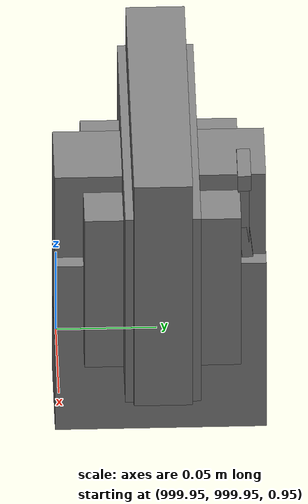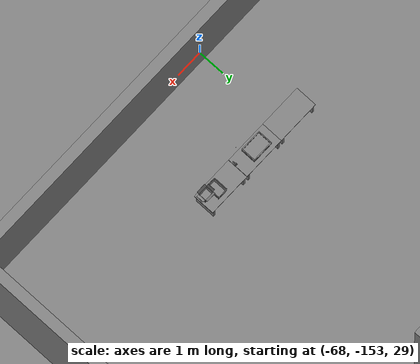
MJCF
<mujoco>
    <option gravity="0.000000000 0.000000000 -9.810000420" timestep="0.0049999999" integrator="implicitfast" density="1.225" viscosity="1.8000001e-05" noslip_iterations="10" iterations="100" sdf_iterations="50">
        <flag multiccd="disable"/>
    </option>
    <size memory="1000M"/>
    <compiler coordinate="local"/>
    <worldbody>
        <light cutoff="30" pos="0 1 1" dir="0 -1 -2"/>
        <light cutoff="30" pos="0 -1 1" dir="0 1 -2"/>
        <body pos="-66.265174866 -149.167404175 31.164838791" euler="-84.409782410 83.389465332 163.357940674" mocap="true" name="spotlight1_SpotLight"/>
        <body pos="1000.000000000 999.999938965 1.000000000" euler="0.000000000 0.000000000 180.000000000" name="openloong_gripper_2f85_fix_base_usda_intelcore_i5">
            <geom contype="1" conaffinity="1" density="1000" type="box" material="" rgba="0.500000000 0.500000000 0.500000000 1.000000000" solimp="0.899999976 0.949999988 0.001000000" friction="1.000000000 0.005000000 0.000100000" solref="0.020000000 1.000000000" margin="0" condim="3" group="0" pos="0.000000000 0.000000000 0.051722717" quat="0.707106709 0.000000000 0.000000000 -0.707106769" size="0.052800000 0.018080002 0.052800000" name="openloong_gripper_2f85_fix_base_usda_geom_67DAE459_6105_4C2A_9B5E_2C190AE79F5B"/>
            <freejoint name="openloong_gripper_2f85_fix_base_usda_intelcore_i5_joint"/>
            <site size="0.005000000 0.005000000 0.005000000" rgba="0.500000000 0.500000000 0.500000000 1.000000000" pos="0.000000000 0.000000000 0.000000000" quat="0.999961913 0.008726534 0.000000000 0.000000000" group="0" type="sphere" name="openloong_gripper_2f85_fix_base_usda_intelcore_i5site"/>
        </body>
        <body pos="1000.000000000 1000.000000000 1.000000000" euler="0.000011953 0.000005123 -179.999984741" name="openloong_gripper_2f85_fix_base_usda_intel_box">
            <geom contype="1" conaffinity="1" density="1000" type="box" material="" rgba="0.500000000 0.500000000 0.500000000 1.000000000" solimp="0.899999976 0.949999988 0.001000000" friction="1.000000000 0.005000000 0.000100000" solref="0.020000000 1.000000000" margin="0" condim="3" group="0" pos="0.000000000 -0.000067139 0.000082284" quat="0.707106709 0.000000225 0.000000253 0.707106650" size="0.052800003 0.025300000 0.052800003" name="openloong_gripper_2f85_fix_base_usda_geom_6EF7153E_0E60_4FC9_A719_3624B9968F4A"/>
            <freejoint name="openloong_gripper_2f85_fix_base_usda_intel_box_joint"/>
            <site size="0.005000000 0.005000000 0.005000000" rgba="0.500000000 0.500000000 0.500000000 1.000000000" pos="0.000000000 0.000000000 0.000000000" quat="0.999961913 0.008726500 0.000000000 0.000000000" group="0" type="sphere" name="openloong_gripper_2f85_fix_base_usda_intel_boxsite"/>
        </body>
        <body pos="-66.029235840 -149.380889893 31.163742065" euler="-139.922897339 -87.684669495 104.605728149" mocap="true" name="spotlight6_SpotLight"/>
        <body pos="1000.000000000 1000.000000000 1.000000000" euler="0.000000000 0.000000000 180.000000000" name="openloong_gripper_2f85_fix_base_usda_wifi_box">
            <geom contype="1" conaffinity="1" density="1000" type="box" material="" rgba="0.500000000 0.500000000 0.500000000 1.000000000" solimp="0.899999976 0.949999988 0.001000000" friction="1.000000000 0.005000000 0.000100000" solref="0.020000000 1.000000000" margin="0" condim="3" group="0" pos="0.000000000 0.000000000 0.058978677" quat="0.000000000 0.000000047 0.000000000 1.000000000" size="0.068499997 0.018999999 0.059000000" name="openloong_gripper_2f85_fix_base_usda_geom_538EA51B_1DCC_4DA0_B705_5AE1074A1A34"/>
            <freejoint name="openloong_gripper_2f85_fix_base_usda_wifi_box_joint"/>
            <site size="0.005000000 0.005000000 0.005000000" rgba="0.500000000 0.500000000 0.500000000 1.000000000" pos="0.000000000 0.000000000 0.000000000" quat="0.999961913 0.008726500 0.000000000 0.000000000" group="0" type="sphere" name="openloong_gripper_2f85_fix_base_usda_wifi_boxsite"/>
        </body>
        <body pos="1000.000000000 1000.000000000 1.000000000" euler="0.000000000 0.000000000 180.000000000" name="openloong_gripper_2f85_fix_base_usda_cpu_fan">
            <geom contype="1" conaffinity="1" density="1000" type="box" material="" rgba="0.500000000 0.500000000 0.500000000 1.000000000" solimp="0.899999976 0.949999988 0.001000000" friction="1.000000000 0.005000000 0.000100000" solref="0.020000000 1.000000000" margin="0" condim="3" group="0" pos="0.000000000 0.000000000 0.070034981" quat="0.000000000 0.000000000 0.000000000 1.000000000" size="0.070700005 0.014699999 0.070700005" name="openloong_gripper_2f85_fix_base_usda_geom_5FDFE9DA_C0C7_4813_A0F7_7894AC5E8166"/>
            <freejoint name="openloong_gripper_2f85_fix_base_usda_cpu_fan_joint"/>
            <site size="0.005000000 0.005000000 0.005000000" rgba="0.500000000 0.500000000 0.500000000 1.000000000" pos="0.000000000 0.000000000 0.000000000" quat="0.999961913 0.008726535 0.000000000 0.000000000" group="0" type="sphere" name="openloong_gripper_2f85_fix_base_usda_cpu_fancsite"/>
        </body>
        <body pos="1000.000000000 1000.000000000 1.000000000" euler="0.000000000 0.000000000 180.000000000" name="openloong_gripper_2f85_fix_base_usda_battery_01">
            <geom contype="1" conaffinity="1" density="1000" type="box" material="" rgba="0.500000000 0.500000000 0.500000000 1.000000000" solimp="0.899999976 0.949999988 0.001000000" friction="1.000000000 0.005000000 0.000100000" solref="0.020000000 1.000000000" margin="0" condim="3" group="0" pos="-0.011123657 -0.041940309 0.101691343" quat="1.000000000 0.000000000 0.000000000 0.000000000" size="0.010800000 0.003375000 0.004725000" name="openloong_gripper_2f85_fix_base_usda_geom_C2473416_1C75_4D00_A01D_8668BCD43B8A"/>
            <geom contype="1" conaffinity="1" density="1000" type="box" material="" rgba="0.500000000 0.500000000 0.500000000 1.000000000" solimp="0.899999976 0.949999988 0.001000000" friction="1.000000000 0.005000000 0.000100000" solref="0.020000000 1.000000000" margin="0" condim="3" group="0" pos="-0.010876465 -0.044247437 0.047066893" quat="0.998702705 -0.050920475 0.000000000 0.000000000" size="0.009450001 0.002700000 0.024975000" name="openloong_gripper_2f85_fix_base_usda_geom_8EEC572C_E67A_4E50_9D3F_8D0E4E148F9C"/>
            <geom contype="1" conaffinity="1" density="1000" type="box" material="" rgba="0.500000000 0.500000000 0.500000000 1.000000000" solimp="0.899999976 0.949999988 0.001000000" friction="1.000000000 0.005000000 0.000100000" solref="0.020000000 1.000000000" margin="0" condim="3" group="0" pos="-0.001235962 -0.000659180 0.047381196" quat="1.000000000 0.000000000 0.000000000 0.000000000" size="0.039420001 0.039150000 0.047250003" name="openloong_gripper_2f85_fix_base_usda_geom_BF2C9364_4968_46F7_984F_6D571CB2D60A"/>
            <geom contype="1" conaffinity="1" density="1000" type="box" material="" rgba="0.500000000 0.500000000 0.500000000 1.000000000" solimp="0.899999976 0.949999988 0.001000000" friction="1.000000000 0.005000000 0.000100000" solref="0.020000000 1.000000000" margin="0" condim="3" group="0" pos="-0.010876465 -0.039138794 0.009851727" quat="1.000000000 0.000000000 0.000000000 0.000000000" size="0.009450001 0.010800000 0.013500000" name="openloong_gripper_2f85_fix_base_usda_geom_4509DF41_ABD8_4FAE_A7CA_54D307CEC1E9"/>
            <geom contype="1" conaffinity="1" density="1000" type="box" material="" rgba="0.500000000 0.500000000 0.500000000 1.000000000" solimp="0.899999976 0.949999988 0.001000000" friction="1.000000000 0.005000000 0.000100000" solref="0.020000000 1.000000000" margin="0" condim="3" group="0" pos="-0.010876465 -0.041528322 0.071508206" quat="1.000000000 0.000000000 0.000000000 0.000000000" size="0.009450001 0.002700000 0.027000001" name="openloong_gripper_2f85_fix_base_usda_geom_DB446A7E_AE56_4734_ACD5_5917911EB507"/>
            <freejoint name="openloong_gripper_2f85_fix_base_usda_battery_01_joint"/>
            <site size="0.005000000 0.005000000 0.005000000" rgba="0.500000000 0.500000000 0.500000000 1.000000000" pos="0.000000000 0.000000000 0.000000000" quat="0.999961913 0.008726500 0.000000000 0.000000000" group="0" type="sphere" name="openloong_gripper_2f85_fix_base_usda_battery_01site"/>
        </body>
        <body pos="-66.037139893 -149.011611938 31.167007446" euler="28.664260864 54.015777588 -141.836929321" mocap="true" name="spotlight4_SpotLight"/>
        <body pos="-64.866622925 -149.383972168 30.183746338" euler="89.999984741 89.999946594 0.000000000" name="openloong_gripper_2f85_fix_base_usda_bluebox_01">
            <geom contype="1" conaffinity="1" density="1000" type="box" material="" rgba="0.500000000 0.500000000 0.500000000 1.000000000" solimp="0.899999976 0.949999988 0.001000000" friction="1.000000000 0.005000000 0.000100000" solref="0.020000000 1.000000000" margin="0" condim="3" group="0" pos="0.276580811 0.187225342 0.000068665" quat="0.707106948 0.000077471 0.707106352 0.000077486" size="0.100000001 0.057999998 0.010000000" name="openloong_gripper_2f85_fix_base_usda_geom_8BF9FB5D_8CC5_42D3_AC7E_28907862FC67"/>
            <geom contype="1" conaffinity="1" density="1000" type="box" material="" rgba="0.500000000 0.500000000 0.500000000 1.000000000" solimp="0.899999976 0.949999988 0.001000000" friction="1.000000000 0.005000000 0.000100000" solref="0.020000000 1.000000000" margin="0" condim="3" group="0" pos="0.000000000 0.002883911 0.000000000" quat="0.999999881 0.000000000 0.000000000 0.000000000" size="0.254000008 0.003000000 0.172000006" name="openloong_gripper_2f85_fix_base_usda_geom_079C9C77_674A_4253_8328_C6046CE57988"/>
            <geom contype="1" conaffinity="1" density="1000" type="box" material="" rgba="0.500000000 0.500000000 0.500000000 1.000000000" solimp="0.899999976 0.949999988 0.001000000" friction="1.000000000 0.005000000 0.000100000" solref="0.020000000 1.000000000" margin="0" condim="3" group="0" pos="0.000000000 0.124874115 0.173484802" quat="0.999796331 0.020176515 -0.000000015 0.000000030" size="0.259999990 0.119999997 0.007000000" name="openloong_gripper_2f85_fix_base_usda_geom_4903C113_4070_4660_A243_0DB69539960C"/>
            <geom contype="1" conaffinity="1" density="1000" type="box" material="" rgba="0.500000000 0.500000000 0.500000000 1.000000000" solimp="0.899999976 0.949999988 0.001000000" friction="1.000000000 0.005000000 0.000100000" solref="0.020000000 1.000000000" margin="0" condim="3" group="0" pos="0.000000000 0.124874115 -0.173469543" quat="0.999796331 -0.020176545 -0.000000015 0.000000000" size="0.259999990 0.119999997 0.007000000" name="openloong_gripper_2f85_fix_base_usda_geom_D332A79F_2277_40B3_BB1B_D790E0BFBF30"/>
            <geom contype="1" conaffinity="1" density="1000" type="box" material="" rgba="0.500000000 0.500000000 0.500000000 1.000000000" solimp="0.899999976 0.949999988 0.001000000" friction="1.000000000 0.005000000 0.000100000" solref="0.020000000 1.000000000" margin="0" condim="3" group="0" pos="0.000000000 0.214008331 0.188980103" quat="0.999912977 0.013176724 0.000000015 0.000000000" size="0.259999990 0.029999999 0.012500000" name="openloong_gripper_2f85_fix_base_usda_geom_F925F86C_BAEC_4B4E_AB1A_885D68667898"/>
            <geom contype="1" conaffinity="1" density="1000" type="box" material="" rgba="0.500000000 0.500000000 0.500000000 1.000000000" solimp="0.899999976 0.949999988 0.001000000" friction="1.000000000 0.005000000 0.000100000" solref="0.020000000 1.000000000" margin="0" condim="3" group="0" pos="-0.258361816 0.125289917 0.001876831" quat="0.702796936 -0.020792112 0.710783124 0.020769298" size="0.189999998 0.119999997 0.009000000" name="openloong_gripper_2f85_fix_base_usda_geom_B56D0F48_79FA_4672_B2E0_4D09DDEE27BB"/>
            <geom contype="1" conaffinity="1" density="1000" type="box" material="" rgba="0.500000000 0.500000000 0.500000000 1.000000000" solimp="0.899999976 0.949999988 0.001000000" friction="1.000000000 0.005000000 0.000100000" solref="0.020000000 1.000000000" margin="0" condim="3" group="0" pos="0.000000000 0.214008331 -0.188980103" quat="0.999912977 -0.013176769 0.000000030 0.000000015" size="0.259999990 0.029999999 0.012500000" name="openloong_gripper_2f85_fix_base_usda_geom_6AC5D8D3_6054_44DD_88F9_13CEB87EC57B"/>
            <geom contype="1" conaffinity="1" density="1000" type="box" material="" rgba="0.500000000 0.500000000 0.500000000 1.000000000" solimp="0.899999976 0.949999988 0.001000000" friction="1.000000000 0.005000000 0.000100000" solref="0.020000000 1.000000000" margin="0" condim="3" group="0" pos="-0.276611328 0.187225342 0.000068665" quat="0.707106650 0.000077441 0.707106709 0.000077456" size="0.100000001 0.057999998 0.010000000" name="openloong_gripper_2f85_fix_base_usda_geom_DDAEE02A_B982_4E4F_A57C_6138BE57BF4D"/>
            <geom contype="1" conaffinity="1" density="1000" type="box" material="" rgba="0.500000000 0.500000000 0.500000000 1.000000000" solimp="0.899999976 0.949999988 0.001000000" friction="1.000000000 0.005000000 0.000100000" solref="0.020000000 1.000000000" margin="0" condim="3" group="0" pos="0.258331299 0.125289917 0.001876831" quat="0.702851415 0.018856421 0.710823774 -0.019329369" size="0.189999998 0.119999997 0.009000000" name="openloong_gripper_2f85_fix_base_usda_geom_47AE1F7A_CB82_49F9_BC8B_56854EB0CCA6"/>
            <freejoint name="openloong_gripper_2f85_fix_base_usda_bluebox_01_joint"/>
            <site size="0.005000000 0.005000000 0.005000000" rgba="0.500000000 0.500000000 0.500000000 1.000000000" pos="0.000000000 0.000000000 0.000000000" quat="0.999961913 0.008726534 0.000000000 0.000000000" group="0" type="sphere" name="openloong_gripper_2f85_fix_base_usda_bluebox_01site"/>
        </body>
        <body pos="-64.496299744 -149.491867065 30.235729218" euler="0.000000000 0.000000000 89.999946594" name="openloong_gripper_2f85_fix_base_usda_cardboardbox_01">
            <geom contype="1" conaffinity="1" density="1000" type="box" material="" rgba="0.500000000 0.500000000 0.500000000 1.000000000" solimp="0.899999976 0.949999988 0.001000000" friction="1.000000000 0.005000000 0.000100000" solref="0.020000000 1.000000000" margin="0" condim="3" group="0" pos="-0.003166199 -0.004086494 0.005052090" quat="1.000000000 0.000000000 0.000000000 0.000000000" size="0.142499998 0.177500010 0.005000000" name="openloong_gripper_2f85_fix_base_usda_geom_8E9F2A20_02B9_48B5_98FC_F6DFEC75F40A"/>
            <geom contype="1" conaffinity="1" density="1000" type="box" material="" rgba="0.500000000 0.500000000 0.500000000 1.000000000" solimp="0.899999976 0.949999988 0.001000000" friction="1.000000000 0.005000000 0.000100000" solref="0.020000000 1.000000000" margin="0" condim="3" group="0" pos="-0.003166199 0.170316696 0.150570869" quat="1.000000000 0.000000000 0.000000000 0.000000000" size="0.142499998 0.005000000 0.149999991" name="openloong_gripper_2f85_fix_base_usda_geom_3B8828AA_CCA4_445F_88D4_2E4D06E12EAC"/>
            <geom contype="1" conaffinity="1" density="1000" type="box" material="" rgba="0.500000000 0.500000000 0.500000000 1.000000000" solimp="0.899999976 0.949999988 0.001000000" friction="1.000000000 0.005000000 0.000100000" solref="0.020000000 1.000000000" margin="0" condim="3" group="0" pos="-0.147399902 -0.005307198 0.150570869" quat="1.000000000 0.000000000 0.000000000 0.000000000" size="0.005000000 0.177500010 0.149999991" name="openloong_gripper_2f85_fix_base_usda_geom_FD6BACC4_E620_4339_AD41_2533BDE5A1D1"/>
            <geom contype="1" conaffinity="1" density="1000" type="box" material="" rgba="0.500000000 0.500000000 0.500000000 1.000000000" solimp="0.899999976 0.949999988 0.001000000" friction="1.000000000 0.005000000 0.000100000" solref="0.020000000 1.000000000" margin="0" condim="3" group="0" pos="0.140275955 -0.005307198 0.150570869" quat="1.000000000 0.000000000 0.000000000 0.000000000" size="0.005000000 0.177500010 0.149999991" name="openloong_gripper_2f85_fix_base_usda_geom_39EE0785_D966_491B_A9CA_A1C81453390E"/>
            <geom contype="1" conaffinity="1" density="1000" type="box" material="" rgba="0.500000000 0.500000000 0.500000000 1.000000000" solimp="0.899999976 0.949999988 0.001000000" friction="1.000000000 0.005000000 0.000100000" solref="0.020000000 1.000000000" margin="0" condim="3" group="0" pos="-0.003166199 -0.181550980 0.150570869" quat="1.000000000 0.000000000 0.000000000 0.000000000" size="0.142499998 0.005000000 0.149999991" name="openloong_gripper_2f85_fix_base_usda_geom_4C5DBD2F_02DE_4B37_A0EF_807EFE3B8014"/>
            <freejoint name="openloong_gripper_2f85_fix_base_usda_cardboardbox_01_joint"/>
            <site size="0.005000000 0.005000000 0.005000000" rgba="0.500000000 0.500000000 0.500000000 1.000000000" pos="0.000000000 0.000000000 0.000000000" quat="0.999961913 0.008726535 0.000000000 0.000000000" group="0" type="sphere" name="openloong_gripper_2f85_fix_base_usda_site_C8639A88_7974_4D5A_A663_698205FB81C1"/>
            <body pos="0.139160156 -0.004048347 0.301930904" euler="-179.999954224 49.383502960 179.999954224" name="openloong_gripper_2f85_fix_base_usda_A1_006">
                <geom contype="1" conaffinity="1" density="1000" type="box" material="" rgba="0.500000000 0.500000000 0.500000000 1.000000000" solimp="0.899999976 0.949999988 0.001000000" friction="1.000000000 0.005000000 0.000100000" solref="0.020000000 1.000000000" margin="0" condim="3" group="0" pos="-0.071587563 0.000009537 0.001745224" quat="0.999999881 0.000000000 0.000000000 0.000000000" size="0.071249999 0.179999992 0.002500000" name="openloong_gripper_2f85_fix_base_usda_geom_6CDDEEFA_5D82_4430_ABA3_293F479A7C55"/>
                <joint armature="0" stiffness="0.07" damping="0.0099999998" axis="0.000000 1.000000 0.000000" type="hinge" name="openloong_gripper_2f85_fix_base_usda_A1_006"/>
            </body>
            <body pos="-0.145902634 -0.004086494 0.301938057" euler="-180.000000000 -60.000011444 -180.000000000" name="openloong_gripper_2f85_fix_base_usda_A2_006">
                <geom contype="1" conaffinity="1" density="1000" type="box" material="" rgba="0.500000000 0.500000000 0.500000000 1.000000000" solimp="0.899999976 0.949999988 0.001000000" friction="1.000000000 0.005000000 0.000100000" solref="0.020000000 1.000000000" margin="0" condim="3" group="0" pos="0.071268082 0.000009537 0.002717972" quat="0.000002921 0.000000000 -0.000000030 0.999999881" size="0.071249999 0.179999992 0.002500000" name="openloong_gripper_2f85_fix_base_usda_geom_C9D91FB4_7DE8_49A0_B3FD_F339900DEC5F"/>
                <joint armature="0" stiffness="0.07" damping="0.0099999998" axis="0.000000 1.000000 0.000000" type="hinge" name="openloong_gripper_2f85_fix_base_usda_A2_006"/>
            </body>
            <body pos="-0.003385544 0.175991058 0.301930904" euler="-125.858116150 -0.000004561 0.000002331" name="openloong_gripper_2f85_fix_base_usda_B2_006">
                <geom contype="1" conaffinity="1" density="1000" type="box" material="" rgba="0.500000000 0.500000000 0.500000000 1.000000000" solimp="0.899999976 0.949999988 0.001000000" friction="1.000000000 0.005000000 0.000100000" solref="0.020000000 1.000000000" margin="0" condim="3" group="0" pos="0.000009537 -0.070939064 -0.002470016" quat="0.999614120 0.027776197 -0.000000015 0.000000030" size="0.137500003 0.064999998 0.005000000" name="openloong_gripper_2f85_fix_base_usda_geom_EFBE34E6_8E1A_43CF_97B2_590C0E442142"/>
                <joint armature="0" stiffness="0.07" damping="0.0099999998" axis="1.000000 0.000000 0.000000" type="hinge" name="openloong_gripper_2f85_fix_base_usda_B2_006"/>
            </body>
            <body pos="-0.003385544 -0.184140205 0.301938057" euler="147.805557251 0.000000000 0.000000000" name="openloong_gripper_2f85_fix_base_usda_B1_006">
                <geom contype="1" conaffinity="1" density="1000" type="box" material="" rgba="0.500000000 0.500000000 0.500000000 1.000000000" solimp="0.899999976 0.949999988 0.001000000" friction="1.000000000 0.005000000 0.000100000" solref="0.020000000 1.000000000" margin="0" condim="3" group="0" pos="-0.000028610 0.070202351 -0.002703667" quat="0.999614179 -0.027776167 0.000000000 0.000000000" size="0.137500003 0.064999998 0.005000000" name="openloong_gripper_2f85_fix_base_usda_geom_350B8258_6DFC_451D_B8C5_C1FF20E0AF9F"/>
                <joint armature="0" stiffness="0.07" damping="0.0099999998" axis="1.000000 0.000000 0.000000" type="hinge" name="openloong_gripper_2f85_fix_base_usda_B1_006"/>
            </body>
        </body>
        <body pos="-65.882858276 -149.481979370 30.229999542" euler="-64.487716675 0.000000000 0.000000000" name="openloong_gripper_2f85_fix_base_usda_Barcode">
            <geom contype="1" conaffinity="1" density="1000" type="box" material="" rgba="0.500000000 0.500000000 0.500000000 1.000000000" solimp="0.899999976 0.949999988 0.001000000" friction="1.000000000 0.005000000 0.000100000" solref="0.020000000 1.000000000" margin="0" condim="3" group="0" pos="0.000000000 0.013038635 0.001419067" quat="0.000000000 0.000000000 0.000000000 1.000000119" size="0.034000002 0.010000000 0.017999999" name="openloong_gripper_2f85_fix_base_usda_geom_7D4157AE_CD16_4BEE_9D4F_D3831C1B27D1"/>
            <geom contype="1" conaffinity="1" density="1000" type="box" material="" rgba="0.500000000 0.500000000 0.500000000 1.000000000" solimp="0.899999976 0.949999988 0.001000000" friction="1.000000000 0.005000000 0.000100000" solref="0.020000000 1.000000000" margin="0" condim="3" group="0" pos="0.000000000 -0.035301208 -0.007095337" quat="0.000000000 0.000000000 -0.043619365 0.999048233" size="0.028999999 0.010000000 0.020000000" name="openloong_gripper_2f85_fix_base_usda_geom_E4F6A857_EFD1_4C67_880A_A0391FE12210"/>
            <geom contype="1" conaffinity="1" density="1000" type="box" material="" rgba="0.500000000 0.500000000 0.500000000 1.000000000" solimp="0.899999976 0.949999988 0.001000000" friction="1.000000000 0.005000000 0.000100000" solref="0.020000000 1.000000000" margin="0" condim="3" group="0" pos="0.000000000 -0.043411255 -0.011749268" quat="0.922262907 0.386563420 0.000000000 0.000000000" size="0.026000001 0.010000000 0.020000000" name="openloong_gripper_2f85_fix_base_usda_geom_2090F9B0_8B67_4E22_A30F_EB696348372E"/>
            <geom contype="1" conaffinity="1" density="1000" type="box" material="" rgba="0.500000000 0.500000000 0.500000000 1.000000000" solimp="0.899999976 0.949999988 0.001000000" friction="1.000000000 0.005000000 0.000100000" solref="0.020000000 1.000000000" margin="0" condim="3" group="0" pos="0.000000000 -0.016967773 -0.031860352" quat="0.000000000 0.000000000 0.000000000 1.000000119" size="0.008000000 0.010000000 0.013000000" name="openloong_gripper_2f85_fix_base_usda_geom_C5AA1D35_A63B_4FF8_BA65_1DCC9BE131B5"/>
            <geom contype="1" conaffinity="1" density="1000" type="box" material="" rgba="0.500000000 0.500000000 0.500000000 1.000000000" solimp="0.899999976 0.949999988 0.001000000" friction="1.000000000 0.005000000 0.000100000" solref="0.020000000 1.000000000" margin="0" condim="3" group="0" pos="0.000000000 -0.001869202 0.000312805" quat="0.953716993 0.300705761 0.000000000 0.000000000" size="0.032000002 0.010000000 0.018999999" name="openloong_gripper_2f85_fix_base_usda_geom_2052981E_4880_42CD_87A6_80C82E920B05"/>
            <geom contype="1" conaffinity="1" density="1000" type="box" material="" rgba="0.500000000 0.500000000 0.500000000 1.000000000" solimp="0.899999976 0.949999988 0.001000000" friction="1.000000000 0.005000000 0.000100000" solref="0.020000000 1.000000000" margin="0" condim="3" group="0" pos="0.000000000 -0.019531250 -0.003173828" quat="0.953716993 0.300705761 0.000000000 0.000000000" size="0.030999999 0.010000000 0.020000000" name="openloong_gripper_2f85_fix_base_usda_geom_E23F2B75_D74C_4C6F_B8C7_6E1E92930DAF"/>
            <geom contype="1" conaffinity="1" density="1000" type="box" material="" rgba="0.500000000 0.500000000 0.500000000 1.000000000" solimp="0.899999976 0.949999988 0.001000000" friction="1.000000000 0.005000000 0.000100000" solref="0.020000000 1.000000000" margin="0" condim="3" group="0" pos="0.000000000 -0.035301208 -0.007095337" quat="0.953716993 0.300705761 0.000000000 0.000000000" size="0.028999999 0.010000000 0.020000000" name="openloong_gripper_2f85_fix_base_usda_geom_5490DF23_01AA_4D52_83CC_A63E3F30B730"/>
            <geom contype="1" conaffinity="1" density="1000" type="box" material="" rgba="0.500000000 0.500000000 0.500000000 1.000000000" solimp="0.899999976 0.949999988 0.001000000" friction="1.000000000 0.005000000 0.000100000" solref="0.020000000 1.000000000" margin="0" condim="3" group="0" pos="0.000000000 -0.042617798 -0.071121216" quat="0.000000000 0.000000000 0.000000000 1.000000119" size="0.013000000 0.021000000 0.059999999" name="openloong_gripper_2f85_fix_base_usda_geom_FCD52C94_BA74_46AA_B498_1E8E6AB214FF"/>
            <freejoint name="openloong_gripper_2f85_fix_base_usda_Barcode_joint"/>
            <site size="0.005000000 0.005000000 0.005000000" rgba="0.500000000 0.500000000 0.500000000 1.000000000" pos="0.000000000 0.000000000 0.000000000" quat="1.000000000 0.000000000 0.000000000 0.000000000" group="0" type="sphere" name="openloong_gripper_2f85_fix_base_usda_Barcode_site"/>
        </body>
        <body pos="-66.745018005 -149.392349243 30.184000015" euler="0.000000000 0.000000000 89.999946594" name="[22330352517889]_Basket_01">
            <geom contype="1" conaffinity="1" density="1000" type="box" material="" rgba="0.500000000 0.500000000 0.500000000 1.000000000" solimp="0.899999976 0.949999988 0.001000000" friction="1.000000000 0.005000000 0.000100000" solref="0.020000000 1.000000000" margin="0" condim="3" group="0" pos="-0.052425385 0.389207840 0.089787483" quat="0.707107008 0.000000000 0.000000000 0.707106411" size="0.014249999 0.014249999 0.059999999" name="[22330352517889]_geom_2323F06F_38BC_46E9_9029_F97ADC6297DB"/>
            <geom contype="1" conaffinity="1" density="1000" type="box" material="" rgba="0.500000000 0.500000000 0.500000000 1.000000000" solimp="0.899999976 0.949999988 0.001000000" friction="1.000000000 0.005000000 0.000100000" solref="0.020000000 1.000000000" margin="0" condim="3" group="0" pos="0.264015198 -0.133043289 0.089787483" quat="0.707107008 0.000000000 0.000000000 0.707106411" size="0.014249999 0.014249999 0.059999999" name="[22330352517889]_geom_FEF7EF35_38AC_44D5_B8DC_457E07ABE996"/>
            <geom contype="1" conaffinity="1" density="1000" type="box" material="" rgba="0.500000000 0.500000000 0.500000000 1.000000000" solimp="0.899999976 0.949999988 0.001000000" friction="1.000000000 0.005000000 0.000100000" solref="0.020000000 1.000000000" margin="0" condim="3" group="0" pos="-0.264015198 -0.265548706 0.089793205" quat="0.707107008 0.000000000 0.000000000 0.707106411" size="0.014249999 0.014249999 0.059999999" name="[22330352517889]_geom_D241D72F_62AB_4D6A_A8E5_A02FC9BEBA5C"/>
            <geom contype="1" conaffinity="1" density="1000" type="box" material="" rgba="0.500000000 0.500000000 0.500000000 1.000000000" solimp="0.899999976 0.949999988 0.001000000" friction="1.000000000 0.005000000 0.000100000" solref="0.020000000 1.000000000" margin="0" condim="3" group="0" pos="-0.160263062 -0.389322281 0.089793205" quat="0.707107008 0.000000000 0.000000000 0.707106411" size="0.014249999 0.014249999 0.059999999" name="[22330352517889]_geom_8EAA5669_70EF_404C_A1AD_B0D9775E0430"/>
            <geom contype="1" conaffinity="1" density="1000" type="box" material="" rgba="0.500000000 0.500000000 0.500000000 1.000000000" solimp="0.899999976 0.949999988 0.001000000" friction="1.000000000 0.005000000 0.000100000" solref="0.020000000 1.000000000" margin="0" condim="3" group="0" pos="0.162265778 -0.389322281 0.089787483" quat="0.707107008 0.000000000 0.000000000 0.707106411" size="0.014249999 0.014249999 0.059999999" name="[22330352517889]_geom_95DB780C_9210_4120_B47A_CE2E0BA301C7"/>
            <geom contype="1" conaffinity="1" density="1000" type="box" material="" rgba="0.500000000 0.500000000 0.500000000 1.000000000" solimp="0.899999976 0.949999988 0.001000000" friction="1.000000000 0.005000000 0.000100000" solref="0.020000000 1.000000000" margin="0" condim="3" group="0" pos="0.264015198 0.389207840 0.089787483" quat="0.707107008 0.000000000 0.000000000 0.707106411" size="0.014249999 0.014249999 0.059999999" name="[22330352517889]_geom_81B577AB_5A9E_48B4_B60B_0BEF52DCE7E5"/>
            <geom contype="1" conaffinity="1" density="1000" type="box" material="" rgba="0.500000000 0.500000000 0.500000000 1.000000000" solimp="0.899999976 0.949999988 0.001000000" friction="1.000000000 0.005000000 0.000100000" solref="0.020000000 1.000000000" margin="0" condim="3" group="0" pos="-0.264015198 -0.133043289 0.089793205" quat="0.707107008 0.000000000 0.000000000 0.707106411" size="0.014249999 0.014249999 0.059999999" name="[22330352517889]_geom_C1986CB5_2C46_4E71_A3D8_3E7B5A15894F"/>
            <geom contype="1" conaffinity="1" density="1000" type="box" material="" rgba="0.500000000 0.500000000 0.500000000 1.000000000" solimp="0.899999976 0.949999988 0.001000000" friction="1.000000000 0.005000000 0.000100000" solref="0.020000000 1.000000000" margin="0" condim="3" group="0" pos="-0.264026642 0.269256592 0.089793205" quat="0.707107008 0.000000000 0.000000000 0.707106411" size="0.014249999 0.014249999 0.059999999" name="[22330352517889]_geom_9F352D05_FF22_4095_AFEE_BBBDE52C45BD"/>
            <geom contype="1" conaffinity="1" density="1000" type="box" material="" rgba="0.500000000 0.500000000 0.500000000 1.000000000" solimp="0.899999976 0.949999988 0.001000000" friction="1.000000000 0.005000000 0.000100000" solref="0.020000000 1.000000000" margin="0" condim="3" group="0" pos="0.054462433 0.389207840 0.089787483" quat="0.707107008 0.000000000 0.000000000 0.707106411" size="0.014249999 0.014249999 0.059999999" name="[22330352517889]_geom_BD87E7D2_1991_45B3_893F_A2EBB32E3E55"/>
            <geom contype="1" conaffinity="1" density="1000" type="box" material="" rgba="0.500000000 0.500000000 0.500000000 1.000000000" solimp="0.899999976 0.949999988 0.001000000" friction="1.000000000 0.005000000 0.000100000" solref="0.020000000 1.000000000" margin="0" condim="3" group="0" pos="0.054462433 -0.389322281 0.089787483" quat="0.707107008 0.000000000 0.000000000 0.707106411" size="0.014249999 0.014249999 0.059999999" name="[22330352517889]_geom_9C001F76_9784_4725_816A_BB758086143A"/>
            <geom contype="1" conaffinity="1" density="1000" type="box" material="" rgba="0.500000000 0.500000000 0.500000000 1.000000000" solimp="0.899999976 0.949999988 0.001000000" friction="1.000000000 0.005000000 0.000100000" solref="0.020000000 1.000000000" margin="0" condim="3" group="0" pos="0.264015198 0.269256592 0.089793205" quat="0.707107008 0.000000000 0.000000000 0.707106411" size="0.014249999 0.014249999 0.059999999" name="[22330352517889]_geom_427EF263_108B_43AE_96CF_18F10676A5EF"/>
            <geom contype="1" conaffinity="1" density="1000" type="box" material="" rgba="0.500000000 0.500000000 0.500000000 1.000000000" solimp="0.899999976 0.949999988 0.001000000" friction="1.000000000 0.005000000 0.000100000" solref="0.020000000 1.000000000" margin="0" condim="3" group="0" pos="0.264015198 -0.389322281 0.089787483" quat="0.707107008 0.000000000 0.000000000 0.707106411" size="0.014249999 0.014249999 0.059999999" name="[22330352517889]_geom_60CB40D8_9A40_464D_8A1E_27F83FA05B7D"/>
            <geom contype="1" conaffinity="1" density="1000" type="box" material="" rgba="0.500000000 0.500000000 0.500000000 1.000000000" solimp="0.899999976 0.949999988 0.001000000" friction="1.000000000 0.005000000 0.000100000" solref="0.020000000 1.000000000" margin="0" condim="3" group="0" pos="0.000000000 0.000000000 0.015998840" quat="0.707107008 0.000000000 0.000000000 0.707106411" size="0.403499991 0.279000014 0.015750000" name="[22330352517889]_geom_CFD5A8D7_F600_4C80_B38A_4D794F4B877D"/>
            <geom contype="1" conaffinity="1" density="1000" type="box" material="" rgba="0.500000000 0.500000000 0.500000000 1.000000000" solimp="0.899999976 0.949999988 0.001000000" friction="1.000000000 0.005000000 0.000100000" solref="0.020000000 1.000000000" margin="0" condim="3" group="0" pos="0.000000000 -0.389476776 0.163619041" quat="0.707107008 0.000000000 0.000000000 0.707106411" size="0.015000000 0.277500004 0.015750000" name="[22330352517889]_geom_702D651A_0900_46C6_B048_65B9BAC39CEA"/>
            <geom contype="1" conaffinity="1" density="1000" type="box" material="" rgba="0.500000000 0.500000000 0.500000000 1.000000000" solimp="0.899999976 0.949999988 0.001000000" friction="1.000000000 0.005000000 0.000100000" solref="0.020000000 1.000000000" margin="0" condim="3" group="0" pos="0.162265778 0.389207840 0.089787483" quat="0.707107008 0.000000000 0.000000000 0.707106411" size="0.014249999 0.014249999 0.059999999" name="[22330352517889]_geom_18B6DA17_A862_41A2_959D_8AB5AE4ECAFF"/>
            <geom contype="1" conaffinity="1" density="1000" type="box" material="" rgba="0.500000000 0.500000000 0.500000000 1.000000000" solimp="0.899999976 0.949999988 0.001000000" friction="1.000000000 0.005000000 0.000100000" solref="0.020000000 1.000000000" margin="0" condim="3" group="0" pos="0.000000000 0.389471054 0.163619041" quat="0.707107008 0.000000000 0.000000000 0.707106411" size="0.015000000 0.277500004 0.015750000" name="[22330352517889]_geom_2B7958C6_2AED_4D8C_A858_3853DB27E796"/>
            <geom contype="1" conaffinity="1" density="1000" type="box" material="" rgba="0.500000000 0.500000000 0.500000000 1.000000000" solimp="0.899999976 0.949999988 0.001000000" friction="1.000000000 0.005000000 0.000100000" solref="0.020000000 1.000000000" margin="0" condim="3" group="0" pos="-0.263511658 0.000000000 0.163619041" quat="0.707107008 0.000000000 0.000000000 0.707106411" size="0.403499991 0.015000000 0.015750000" name="[22330352517889]_geom_FE8D0C17_23EE_4775_8A29_3835BC6BE92F"/>
            <geom contype="1" conaffinity="1" density="1000" type="box" material="" rgba="0.500000000 0.500000000 0.500000000 1.000000000" solimp="0.899999976 0.949999988 0.001000000" friction="1.000000000 0.005000000 0.000100000" solref="0.020000000 1.000000000" margin="0" condim="3" group="0" pos="-0.264015198 0.141334534 0.089793205" quat="0.707107008 0.000000000 0.000000000 0.707106411" size="0.014249999 0.014249999 0.059999999" name="[22330352517889]_geom_69499B8C_941C_4F98_B3A8_AC6F1519E136"/>
            <geom contype="1" conaffinity="1" density="1000" type="box" material="" rgba="0.500000000 0.500000000 0.500000000 1.000000000" solimp="0.899999976 0.949999988 0.001000000" friction="1.000000000 0.005000000 0.000100000" solref="0.020000000 1.000000000" margin="0" condim="3" group="0" pos="0.264015198 -0.265548706 0.089787483" quat="0.707107008 0.000000000 0.000000000 0.707106411" size="0.014249999 0.014249999 0.059999999" name="[22330352517889]_geom_0F8B002F_3DF5_447D_BBC1_33C2CC175DE6"/>
            <geom contype="1" conaffinity="1" density="1000" type="box" material="" rgba="0.500000000 0.500000000 0.500000000 1.000000000" solimp="0.899999976 0.949999988 0.001000000" friction="1.000000000 0.005000000 0.000100000" solref="0.020000000 1.000000000" margin="0" condim="3" group="0" pos="-0.160263062 0.389207840 0.089787483" quat="0.707107008 0.000000000 0.000000000 0.707106411" size="0.014249999 0.014249999 0.059999999" name="[22330352517889]_geom_C3777216_7019_42B3_A815_4FA387AB6199"/>
            <geom contype="1" conaffinity="1" density="1000" type="box" material="" rgba="0.500000000 0.500000000 0.500000000 1.000000000" solimp="0.899999976 0.949999988 0.001000000" friction="1.000000000 0.005000000 0.000100000" solref="0.020000000 1.000000000" margin="0" condim="3" group="0" pos="-0.052425385 -0.389322281 0.089787483" quat="0.707107008 0.000000000 0.000000000 0.707106411" size="0.014249999 0.014249999 0.059999999" name="[22330352517889]_geom_3EA28985_7084_42F9_A861_C8EAC5F827B8"/>
            <geom contype="1" conaffinity="1" density="1000" type="box" material="" rgba="0.500000000 0.500000000 0.500000000 1.000000000" solimp="0.899999976 0.949999988 0.001000000" friction="1.000000000 0.005000000 0.000100000" solref="0.020000000 1.000000000" margin="0" condim="3" group="0" pos="-0.264026642 -0.389322281 0.089793205" quat="0.707107008 0.000000000 0.000000000 0.707106411" size="0.014249999 0.014249999 0.059999999" name="[22330352517889]_geom_960042AA_2626_4B61_948A_A90952150A23"/>
            <geom contype="1" conaffinity="1" density="1000" type="box" material="" rgba="0.500000000 0.500000000 0.500000000 1.000000000" solimp="0.899999976 0.949999988 0.001000000" friction="1.000000000 0.005000000 0.000100000" solref="0.020000000 1.000000000" margin="0" condim="3" group="0" pos="0.264015198 0.141334534 0.089787483" quat="0.707107008 0.000000000 0.000000000 0.707106411" size="0.014249999 0.014249999 0.059999999" name="[22330352517889]_geom_D3F660B0_202A_4584_8ACD_AD27503B45DD"/>
            <geom contype="1" conaffinity="1" density="1000" type="box" material="" rgba="0.500000000 0.500000000 0.500000000 1.000000000" solimp="0.899999976 0.949999988 0.001000000" friction="1.000000000 0.005000000 0.000100000" solref="0.020000000 1.000000000" margin="0" condim="3" group="0" pos="-0.264015198 0.389207840 0.089793205" quat="0.707107008 0.000000000 0.000000000 0.707106411" size="0.014249999 0.014249999 0.059999999" name="[22330352517889]_geom_16C14A86_0609_45D1_A82D_AAD0B74A2C46"/>
            <geom contype="1" conaffinity="1" density="1000" type="box" material="" rgba="0.500000000 0.500000000 0.500000000 1.000000000" solimp="0.899999976 0.949999988 0.001000000" friction="1.000000000 0.005000000 0.000100000" solref="0.020000000 1.000000000" margin="0" condim="3" group="0" pos="0.264015198 0.004480362 0.089787483" quat="0.707107008 0.000000000 0.000000000 0.707106411" size="0.014249999 0.014249999 0.059999999" name="[22330352517889]_geom_82601077_576E_4CED_B16D_F4C91641510D"/>
            <geom contype="1" conaffinity="1" density="1000" type="box" material="" rgba="0.500000000 0.500000000 0.500000000 1.000000000" solimp="0.899999976 0.949999988 0.001000000" friction="1.000000000 0.005000000 0.000100000" solref="0.020000000 1.000000000" margin="0" condim="3" group="0" pos="0.263694763 -0.000011444 0.163619041" quat="0.707107008 0.000000000 0.000000000 0.707106411" size="0.403499991 0.015000000 0.015750000" name="[22330352517889]_geom_0D1666B1_DD8F_4C19_B449_053B8C6A1A09"/>
            <geom contype="1" conaffinity="1" density="1000" type="box" material="" rgba="0.500000000 0.500000000 0.500000000 1.000000000" solimp="0.899999976 0.949999988 0.001000000" friction="1.000000000 0.005000000 0.000100000" solref="0.020000000 1.000000000" margin="0" condim="3" group="0" pos="-0.264015198 0.004480362 0.089793205" quat="0.707107008 0.000000000 0.000000000 0.707106411" size="0.014249999 0.014249999 0.059999999" name="[22330352517889]_geom_FB691CF3_2B95_458B_AEA4_E204789C466D"/>
            <freejoint name="[22330352517889]_joint_E2B542A0_67C8_43AE_B1C4_8438DDE65C41"/>
        </body>
        <body pos="0.000000000 0.000000000 0.000000000" euler="0.000000000 0.000000000 0.000000000" name="Static Objects_Static Objects">
            <geom contype="1" conaffinity="1" density="1000" type="box" material="" rgba="0.500000000 0.500000000 0.500000000 1.000000000" solimp="0.899999976 0.949999988 0.001000000" friction="1.000000000 0.005000000 0.000100000" solref="0.020000000 1.000000000" margin="0" condim="3" group="0" pos="-67.544113159 -149.365814209 29.727830887" quat="0.500000417 0.499999970 0.499999553 0.499999970" size="0.381000012 0.319999993 0.041000001" name="Static Objects_geom_114983C1_2B4E_4235_A6E4_862DEEA1C6A9"/>
            <geom contype="1" conaffinity="1" density="1000" type="box" material="" rgba="0.500000000 0.500000000 0.500000000 1.000000000" solimp="0.899999976 0.949999988 0.001000000" friction="1.000000000 0.005000000 0.000100000" solref="0.020000000 1.000000000" margin="0" condim="3" group="0" pos="-68.239501953 -149.365814209 30.086868286" quat="0.500000417 0.499999970 0.499999553 0.499999970" size="0.370999992 0.039500002 0.745000005" name="Static Objects_geom_07703B97_6AD1_4D24_8E41_DBB78C9CADFA"/>
            <geom contype="1" conaffinity="1" density="1000" type="box" material="" rgba="0.500000000 0.500000000 0.500000000 1.000000000" solimp="0.899999976 0.949999988 0.001000000" friction="1.000000000 0.005000000 0.000100000" solref="0.020000000 1.000000000" margin="0" condim="3" group="0" pos="-68.239501953 -149.365814209 30.147235870" quat="0.500000417 0.499999970 0.499999553 0.499999970" size="0.400000006 0.022000000 0.800000012" name="Static Objects_geom_57EC92BB_FE3F_4B3C_A2E8_4D56AAF74C1C"/>
            <geom contype="1" conaffinity="1" density="1000" type="box" material="" rgba="0.500000000 0.500000000 0.500000000 1.000000000" solimp="0.899999976 0.949999988 0.001000000" friction="1.000000000 0.005000000 0.000100000" solref="0.020000000 1.000000000" margin="0" condim="3" group="0" pos="-68.934890747 -149.365814209 29.727830887" quat="0.500000417 0.499999970 0.499999553 0.499999970" size="0.381000012 0.319999993 0.041000001" name="Static Objects_geom_8D74C454_8DAE_4EAF_8119_551511AD82AF"/>
            <geom contype="1" conaffinity="1" density="1000" type="box" material="" rgba="0.500000000 0.500000000 0.500000000 1.000000000" solimp="0.899999976 0.949999988 0.001000000" friction="1.000000000 0.005000000 0.000100000" solref="0.020000000 1.000000000" margin="0" condim="3" group="0" pos="-68.239501953 -149.365814209 29.561563492" quat="0.500000417 0.499999970 0.499999553 0.499999970" size="0.020000000 0.022000000 0.660000026" name="Static Objects_geom_7CF14E73_5362_4A3C_970D_117ACBCF2604"/>
            <geom contype="1" conaffinity="1" density="1000" type="box" material="" rgba="0.500000000 0.500000000 0.500000000 1.000000000" solimp="0.899999976 0.949999988 0.001000000" friction="1.000000000 0.005000000 0.000100000" solref="0.020000000 1.000000000" margin="0" condim="3" group="0" pos="-65.945671082 -149.365814209 29.727830887" quat="0.500000417 0.499999970 0.499999553 0.499999970" size="0.381000012 0.319999993 0.041000001" name="Static Objects_geom_A6D4D9AF_16EA_401C_AF85_3E7D0C769E8C"/>
            <geom contype="1" conaffinity="1" density="1000" type="box" material="" rgba="0.500000000 0.500000000 0.500000000 1.000000000" solimp="0.899999976 0.949999988 0.001000000" friction="1.000000000 0.005000000 0.000100000" solref="0.020000000 1.000000000" margin="0" condim="3" group="0" pos="-66.641059875 -149.365814209 30.086868286" quat="0.500000417 0.499999970 0.499999553 0.499999970" size="0.370999992 0.039500002 0.745000005" name="Static Objects_geom_F54C78FD_B396_4841_9EA6_32ACB5DCCB78"/>
            <geom contype="1" conaffinity="1" density="1000" type="box" material="" rgba="0.500000000 0.500000000 0.500000000 1.000000000" solimp="0.899999976 0.949999988 0.001000000" friction="1.000000000 0.005000000 0.000100000" solref="0.020000000 1.000000000" margin="0" condim="3" group="0" pos="-66.641059875 -149.365814209 30.147235870" quat="0.500000417 0.499999970 0.499999553 0.499999970" size="0.400000006 0.022000000 0.800000012" name="Static Objects_geom_11A25F46_728E_462D_889B_67306559BF76"/>
            <geom contype="1" conaffinity="1" density="1000" type="box" material="" rgba="0.500000000 0.500000000 0.500000000 1.000000000" solimp="0.899999976 0.949999988 0.001000000" friction="1.000000000 0.005000000 0.000100000" solref="0.020000000 1.000000000" margin="0" condim="3" group="0" pos="-67.336448669 -149.365814209 29.727830887" quat="0.500000417 0.499999970 0.499999553 0.499999970" size="0.381000012 0.319999993 0.041000001" name="Static Objects_geom_93DAB5EE_3A50_4C04_B320_2C537F018BE2"/>
            <geom contype="1" conaffinity="1" density="1000" type="box" material="" rgba="0.500000000 0.500000000 0.500000000 1.000000000" solimp="0.899999976 0.949999988 0.001000000" friction="1.000000000 0.005000000 0.000100000" solref="0.020000000 1.000000000" margin="0" condim="3" group="0" pos="-66.641059875 -149.365814209 29.561563492" quat="0.500000417 0.499999970 0.499999553 0.499999970" size="0.020000000 0.022000000 0.660000026" name="Static Objects_geom_8C459BC8_2364_4748_BFDE_1A232A172364"/>
            <geom contype="1" conaffinity="1" density="1000" type="box" material="" rgba="0.500000000 0.500000000 0.500000000 1.000000000" solimp="0.899999976 0.949999988 0.001000000" friction="1.000000000 0.005000000 0.000100000" solref="0.020000000 1.000000000" margin="0" condim="3" group="0" pos="-64.338577271 -149.365814209 29.727830887" quat="0.500000417 0.499999970 0.499999553 0.499999970" size="0.381000012 0.319999993 0.041000001" name="Static Objects_geom_64EDB38D_9186_4F48_8FFE_A067AC551267"/>
            <geom contype="1" conaffinity="1" density="1000" type="box" material="" rgba="0.500000000 0.500000000 0.500000000 1.000000000" solimp="0.899999976 0.949999988 0.001000000" friction="1.000000000 0.005000000 0.000100000" solref="0.020000000 1.000000000" margin="0" condim="3" group="0" pos="-65.033966064 -149.365814209 30.086868286" quat="0.500000417 0.499999970 0.499999553 0.499999970" size="0.370999992 0.039500002 0.745000005" name="Static Objects_geom_B3CCD5BF_FED4_45F3_A068_015C3330F0F1"/>
            <geom contype="1" conaffinity="1" density="1000" type="box" material="" rgba="0.500000000 0.500000000 0.500000000 1.000000000" solimp="0.899999976 0.949999988 0.001000000" friction="1.000000000 0.005000000 0.000100000" solref="0.020000000 1.000000000" margin="0" condim="3" group="0" pos="-65.033966064 -149.365814209 30.147235870" quat="0.500000417 0.499999970 0.499999553 0.499999970" size="0.400000006 0.022000000 0.800000012" name="Static Objects_geom_EC4471D3_E5B3_48CA_916B_984E5629086B"/>
            <geom contype="1" conaffinity="1" density="1000" type="box" material="" rgba="0.500000000 0.500000000 0.500000000 1.000000000" solimp="0.899999976 0.949999988 0.001000000" friction="1.000000000 0.005000000 0.000100000" solref="0.020000000 1.000000000" margin="0" condim="3" group="0" pos="-65.729354858 -149.365814209 29.727830887" quat="0.500000417 0.499999970 0.499999553 0.499999970" size="0.381000012 0.319999993 0.041000001" name="Static Objects_geom_8E6423C2_F4D0_415E_A10A_407DE99221E3"/>
            <geom contype="1" conaffinity="1" density="1000" type="box" material="" rgba="0.500000000 0.500000000 0.500000000 1.000000000" solimp="0.899999976 0.949999988 0.001000000" friction="1.000000000 0.005000000 0.000100000" solref="0.020000000 1.000000000" margin="0" condim="3" group="0" pos="-65.033966064 -149.365814209 29.561563492" quat="0.500000417 0.499999970 0.499999553 0.499999970" size="0.020000000 0.022000000 0.660000026" name="Static Objects_geom_192FE506_56CF_41E5_9293_6BDD715B2AD7"/>
            <geom contype="1" conaffinity="1" density="1000" type="box" material="" rgba="0.500000000 0.500000000 0.500000000 1.000000000" solimp="0.899999976 0.949999988 0.001000000" friction="1.000000000 0.005000000 0.000100000" solref="0.020000000 1.000000000" margin="0" condim="3" group="0" pos="-61.754566193 -137.853729248 33.906845093" quat="0.707107067 0.000000000 0.000000000 0.707106471" size="0.759999990 0.759999990 4.500000000" name="Static Objects_geom_82FDEF69_6682_4C06_B097_0D248225A051"/>
            <geom contype="1" conaffinity="1" density="1000" type="box" material="" rgba="0.500000000 0.500000000 0.500000000 1.000000000" solimp="0.899999976 0.949999988 0.001000000" friction="1.000000000 0.005000000 0.000100000" solref="0.020000000 1.000000000" margin="0" condim="3" group="0" pos="-57.511135101 -144.927108765 31.707921982" quat="1.000000000 0.000000000 0.000000000 0.000000000" size="0.200000003 8.000000000 2.299999952" name="Static Objects_geom_74E7572D_6B19_4471_85AD_1F72BFB6F6B4"/>
            <geom contype="1" conaffinity="1" density="1000" type="box" material="" rgba="0.500000000 0.500000000 0.500000000 1.000000000" solimp="0.899999976 0.949999988 0.001000000" friction="1.000000000 0.005000000 0.000100000" solref="0.020000000 1.000000000" margin="0" condim="3" group="0" pos="-80.517646790 -157.574050903 31.688196182" quat="0.707107067 0.000000000 0.000000000 0.707106471" size="0.600000024 0.600000024 2.299999952" name="Static Objects_geom_DCCA4E09_AA92_4750_8694_7C395852018E"/>
            <geom contype="1" conaffinity="1" density="1000" type="box" material="" rgba="0.500000000 0.500000000 0.500000000 1.000000000" solimp="0.899999976 0.949999988 0.001000000" friction="1.000000000 0.005000000 0.000100000" solref="0.020000000 1.000000000" margin="0" condim="3" group="0" pos="-80.711044312 -147.414932251 31.666158676" quat="1.000000000 0.000000000 0.000000000 0.000000000" size="0.200000003 10.000000000 2.299999952" name="Static Objects_geom_E2A81D5C_D5BC_416D_BED6_42254870F22A"/>
            <geom contype="1" conaffinity="1" density="1000" type="box" material="" rgba="0.500000000 0.500000000 0.500000000 1.000000000" solimp="0.899999976 0.949999988 0.001000000" friction="1.000000000 0.005000000 0.000100000" solref="0.020000000 1.000000000" margin="0" condim="3" group="0" pos="-57.687217712 -137.434692383 31.688196182" quat="0.707107067 0.000000000 0.000000000 0.707106471" size="0.600000024 0.600000024 2.299999952" name="Static Objects_geom_91F7DE84_926A_45B6_8340_E11E8F6B08D1"/>
            <geom contype="1" conaffinity="1" density="1000" type="box" material="" rgba="0.500000000 0.500000000 0.500000000 1.000000000" solimp="0.899999976 0.949999988 0.001000000" friction="1.000000000 0.005000000 0.000100000" solref="0.020000000 1.000000000" margin="0" condim="3" group="0" pos="-69.537033081 -140.263229370 31.714921951" quat="0.707107067 0.000000000 0.000000000 0.707106471" size="0.759999990 4.500000000 2.299999952" name="Static Objects_geom_4B108A4F_E776_4F51_9D87_00BF0EC89704"/>
            <geom contype="1" conaffinity="1" density="1000" type="box" material="" rgba="0.500000000 0.500000000 0.500000000 1.000000000" solimp="0.899999976 0.949999988 0.001000000" friction="1.000000000 0.005000000 0.000100000" solref="0.020000000 1.000000000" margin="0" condim="3" group="0" pos="-80.073638916 -137.853713989 33.906845093" quat="0.707107067 0.000000000 0.000000000 0.707106471" size="0.759999990 0.759999990 4.500000000" name="Static Objects_geom_78C68DDC_E1AA_45DB_94AC_F030E9B00798"/>
            <geom contype="1" conaffinity="1" density="1000" type="box" material="" rgba="0.500000000 0.500000000 0.500000000 1.000000000" solimp="0.899999976 0.949999988 0.001000000" friction="1.000000000 0.005000000 0.000100000" solref="0.020000000 1.000000000" margin="0" condim="3" group="0" pos="-73.406707764 -155.734664917 31.707921982" quat="1.000000000 0.000000000 0.000000000 0.000000000" size="0.200000003 3.000000000 2.299999952" name="Static Objects_geom_87423BD3_157A_442F_ACB9_A34D041AB255"/>
            <geom contype="1" conaffinity="1" density="1000" type="box" material="" rgba="0.500000000 0.500000000 0.500000000 1.000000000" solimp="0.899999976 0.949999988 0.001000000" friction="1.000000000 0.005000000 0.000100000" solref="0.020000000 1.000000000" margin="0" condim="3" group="0" pos="-68.497543335 -137.448257446 31.707921982" quat="0.707107067 0.000000000 0.000000000 0.707106471" size="0.200000003 14.000000000 2.299999952" name="Static Objects_geom_AA9A0725_9861_45C4_8260_39D051BF3965"/>
            <geom contype="1" conaffinity="1" density="1000" type="cylinder" material="" rgba="0.500000000 0.500000000 0.500000000 1.000000000" solimp="0.899999976 0.949999988 0.001000000" friction="1.000000000 0.005000000 0.000100000" solref="0.020000000 1.000000000" margin="0" condim="3" group="0" pos="-68.868522644 -142.134506226 31.711090088" quat="0.707107067 0.000000000 0.000000000 0.707106471" size="0.509999990 2.299999952 1.000000000" name="Static Objects_geom_69E95AA3_41ED_4F92_B83D_EAEAC9B4C361"/>
            <geom contype="1" conaffinity="1" density="1000" type="plane" material="" rgba="0.500000000 0.500000000 0.500000000 1.000000000" solimp="0.899999976 0.949999988 0.001000000" friction="1.000000000 0.005000000 0.000100000" solref="0.020000000 1.000000000" margin="0" condim="3" group="0" pos="-72.873703003 -147.131927490 29.409669876" quat="1.000000000 0.000000000 0.000000000 0.000000000" size="18.000000000 14.000000000 1.000000000" name="Static Objects_geom_01D79D29_56F6_46F4_9B08_18E5A93D4875"/>
            <geom contype="1" conaffinity="1" density="1000" type="box" material="" rgba="0.500000000 0.500000000 0.500000000 1.000000000" solimp="0.899999976 0.949999988 0.001000000" friction="1.000000000 0.005000000 0.000100000" solref="0.020000000 1.000000000" margin="0" condim="3" group="0" pos="-79.943580627 -157.782272339 31.707921982" quat="0.707107067 0.000000000 0.000000000 0.707106471" size="0.200000003 7.000000000 2.299999952" name="Static Objects_geom_3C857528_8279_40B1_A4D2_2A76A3B0C2DC"/>
            <geom contype="1" conaffinity="1" density="1000" type="box" material="" rgba="0.500000000 0.500000000 0.500000000 1.000000000" solimp="0.899999976 0.949999988 0.001000000" friction="1.000000000 0.005000000 0.000100000" solref="0.020000000 1.000000000" margin="0" condim="3" group="0" pos="-65.421028137 -152.903442383 31.707921982" quat="0.707107067 0.000000000 0.000000000 0.707106471" size="0.200000003 7.800000191 2.299999952" name="Static Objects_geom_23CF9945_FCE7_4953_AD31_D4C04158525E"/>
            <geom contype="1" conaffinity="1" density="1000" type="box" material="" rgba="0.500000000 0.500000000 0.500000000 1.000000000" solimp="0.899999976 0.949999988 0.001000000" friction="1.000000000 0.005000000 0.000100000" solref="0.020000000 1.000000000" margin="0" condim="3" group="0" pos="-74.776908875 -149.964416504 31.688196182" quat="1.000000000 0.000000000 0.000000000 0.000000000" size="0.600000024 0.409999996 2.299999952" name="Static Objects_geom_AFB2A086_6233_430E_B583_5C3A2F586736"/>
            <geom contype="1" conaffinity="1" density="1000" type="cylinder" material="" rgba="0.500000000 0.500000000 0.500000000 1.000000000" solimp="0.899999976 0.949999988 0.001000000" friction="1.000000000 0.005000000 0.000100000" solref="0.020000000 1.000000000" margin="0" condim="3" group="0" pos="-60.161884308 -142.134506226 31.711090088" quat="0.707107067 0.000000000 0.000000000 0.707106471" size="0.509999990 2.299999952 1.000000000" name="Static Objects_geom_95C58E61_5D19_4D3D_9C1D_B4B32BE3A8E2"/>
            <geom contype="1" conaffinity="1" density="1000" type="cylinder" material="" rgba="0.500000000 0.500000000 0.500000000 1.000000000" solimp="0.899999976 0.949999988 0.001000000" friction="1.000000000 0.005000000 0.000100000" solref="0.020000000 1.000000000" margin="0" condim="3" group="0" pos="-75.382453918 -149.963455200 31.711090088" quat="0.707107067 0.000000000 0.000000000 0.707106471" size="0.409999996 2.299999952 1.000000000" name="Static Objects_geom_6A49842A_69A6_4C74_81B7_BC8E26651D75"/>
            <geom contype="1" conaffinity="1" density="1000" type="cylinder" material="" rgba="0.500000000 0.500000000 0.500000000 1.000000000" solimp="0.899999976 0.949999988 0.001000000" friction="1.000000000 0.005000000 0.000100000" solref="0.020000000 1.000000000" margin="0" condim="3" group="0" pos="-74.154960632 -149.963455200 31.711090088" quat="0.707107067 0.000000000 0.000000000 0.707106471" size="0.409999996 2.299999952 1.000000000" name="Static Objects_geom_AC3E17C1_3A22_4E99_BCB4_09A0AD8DC78C"/>
            <geom contype="1" conaffinity="1" density="1000" type="cylinder" material="" rgba="0.500000000 0.500000000 0.500000000 1.000000000" solimp="0.899999976 0.949999988 0.001000000" friction="1.000000000 0.005000000 0.000100000" solref="0.020000000 1.000000000" margin="0" condim="3" group="0" pos="-77.566612244 -142.134506226 31.711090088" quat="0.707107067 0.000000000 0.000000000 0.707106471" size="0.509999990 2.299999952 1.000000000" name="Static Objects_geom_ABCD6E1F_E311_4E2C_A622_7465B9BCEC5E"/>
        </body>
        <body pos="-66.291030884 -149.869689941 29.018842697" euler="0.000000000 0.000000000 89.999946594" mocap="true" name="openloong_gripper_2f85_fix_base_usda_leftHandMocap"/>
        <body pos="-66.291030884 -149.869689941 29.018842697" euler="0.000000000 0.000000000 89.999946594" mocap="true" name="openloong_gripper_2f85_fix_base_usda_rightHandMocap"/>
        <body pos="-66.291030884 -149.869689941 30.218843460" euler="0.000000000 0.000000000 89.999946594" name="openloong_gripper_2f85_fix_base_usda_base_link">
            <geom contype="1" conaffinity="1" density="1000" type="mesh" material="" rgba="0.783999979 0.783999979 0.783999979 1.000000000" solimp="0.899999976 0.949999988 0.001000000" friction="1.000000000 0.005000000 0.000100000" solref="0.020000000 1.000000000" margin="0" condim="3" group="3" mesh="base_link" pos="0.000000000 0.000000000 0.000000000" quat="1.000000000 0.000000000 0.000000000 0.000000000" size="1.000000000 1.000000000 1.000000000" name="openloong_gripper_2f85_fix_base_usda__geom_7_F7DD262C_98F1_4A79_A5DB_1B04B157427A"/>
            <site size="0.005000000 0.005000000 0.005000000" rgba="0.500000000 0.500000000 0.500000000 1.000000000" pos="0.000000000 0.000000000 0.000000000" quat="1.000000000 0.000000000 0.000000000 0.000000000" group="0" type="sphere" name="openloong_gripper_2f85_fix_base_usda_imu"/>
            <inertial mass="22.447001" pos="-0.005664100 -0.001336700 0.238289997" diaginertia="0.374352545 0.277180195 0.220617250" quat="0.999247074 0.035235517 -0.015086859 0.006023135"/>
            <body pos="0.000000000 0.000000000 0.299997330" euler="0.000000000 0.000000000 0.000000000" name="openloong_gripper_2f85_fix_base_usda_dummy_body">
                <geom contype="1" conaffinity="1" density="1000" type="sphere" material="" rgba="0.783999979 0.783999979 0.783999979 1.000000000" solimp="0.899999976 0.949999988 0.001000000" friction="1.000000000 0.005000000 0.000100000" solref="0.020000000 1.000000000" margin="0" condim="3" group="3" pos="0.000000000 0.000000000 0.000000000" quat="1.000000000 0.000000000 0.000000000 0.000000000" size="0.010000000 0.000000000 0.000000000" name="openloong_gripper_2f85_fix_base_usda__geom_8_15AD8D00_C2C6_4DE7_AE05_9EB9942E6040"/>
                <joint armature="0.0099999998" stiffness="0" damping="0.1" axis="0.000000 0.000000 1.000000" type="hinge" name="openloong_gripper_2f85_fix_base_usda_dummy_joint"/>
                <site size="0.010000000 0.005000000 0.005000000" rgba="0.500000000 0.500000000 0.500000000 1.000000000" pos="0.000000000 0.000000000 0.000000000" quat="1.000000000 0.000000000 0.000000000 0.000000000" group="3" type="sphere" name="openloong_gripper_2f85_fix_base_usda_dummy_site"/>
            </body>
            <body pos="0.009002686 0.000000000 0.406400681" euler="0.000000000 0.000000000 0.000000000" name="openloong_gripper_2f85_fix_base_usda_Link_head_yaw">
                <geom contype="1" conaffinity="1" density="1000" type="mesh" material="" rgba="0.783999979 0.783999979 0.783999979 1.000000000" solimp="0.899999976 0.949999988 0.001000000" friction="1.000000000 0.005000000 0.000100000" solref="0.020000000 1.000000000" margin="0" condim="3" group="3" mesh="Link_head_yaw" pos="0.000000000 0.000000000 0.000000000" quat="1.000000000 0.000000000 0.000000000 0.000000000" size="1.000000000 1.000000000 1.000000000" name="openloong_gripper_2f85_fix_base_usda__geom_10_B6A51221_945A_4623_B354_C4DCC13709BA"/>
                <inertial mass="0.84249002" pos="0.000000000 -0.002081400 0.044801001" diaginertia="0.000700588 0.000629000 0.000553812" quat="0.706933022 -0.015675601 0.015677100 0.706933022"/>
                <body pos="0.000000000 -0.034599304 0.048500061" euler="0.000000000 0.000000000 0.000000000" name="openloong_gripper_2f85_fix_base_usda_Link_head_pitch">
                    <geom contype="1" conaffinity="1" density="1000" type="mesh" material="" rgba="0.783999979 0.783999979 0.783999979 1.000000000" solimp="0.899999976 0.949999988 0.001000000" friction="1.000000000 0.005000000 0.000100000" solref="0.020000000 1.000000000" margin="0" condim="3" group="3" mesh="Link_head_pitch" pos="0.000000000 0.000000000 0.000000000" quat="1.000000000 0.000000000 0.000000000 0.000000000" size="1.000000000 1.000000000 1.000000000" name="openloong_gripper_2f85_fix_base_usda__geom_12_292CA37E_F0D1_41ED_88FD_21907955F70E"/>
                    <inertial mass="1.3943" pos="0.020569000 0.033004001 0.125000000" diaginertia="0.006381400 0.006289940 0.004481460" quat="0.973390222 0.008406822 0.228157058 0.019624906"/>
                    <body pos="0.000000000 0.029998779 0.000000000" euler="0.000000000 0.000000000 0.000000000" name="openloong_gripper_2f85_fix_base_usda_neck_center_body">
                        <site size="0.010000000 0.005000000 0.005000000" rgba="0.500000000 0.500000000 0.500000000 1.000000000" pos="0.000000000 0.000000000 0.000000000" quat="1.000000000 0.000000000 0.000000000 0.000000000" group="3" type="sphere" name="openloong_gripper_2f85_fix_base_usda_neck_center_site"/>
                        <body pos="0.020004272 0.000000000 0.149999619" euler="-0.000002229 39.998176575 -90.000205994" name="openloong_gripper_2f85_fix_base_usda_camera_head">
                            <site size="0.010000000 0.005000000 0.005000000" rgba="0.500000000 0.500000000 0.500000000 1.000000000" pos="0.000000000 0.000000000 0.000000000" quat="1.000000000 0.000000000 0.000000000 0.000000000" group="3" type="sphere" name="openloong_gripper_2f85_fix_base_usda_camera_head_site"/>
                        </body>
                    </body>
                </body>
            </body>
            <body pos="0.003997803 -0.161598206 0.392200470" euler="0.000000000 0.000000000 0.000000000" name="openloong_gripper_2f85_fix_base_usda_Link_arm_r_01">
                <geom contype="1" conaffinity="1" density="1000" type="mesh" material="" rgba="0.783999979 0.783999979 0.783999979 1.000000000" solimp="0.899999976 0.949999988 0.001000000" friction="1.000000000 0.005000000 0.000100000" solref="0.020000000 1.000000000" margin="0" condim="3" group="3" mesh="Link_arm_r_01" pos="0.000000000 0.000000000 0.000000000" quat="1.000000000 0.000000000 0.000000000 0.000000000" size="1.000000000 1.000000000 1.000000000" name="openloong_gripper_2f85_fix_base_usda__geom_14_036A0280_D160_4C9A_85D7_F6C08735642B"/>
                <joint armature="0.0099999998" stiffness="0" damping="1" axis="0.000000 -1.000000 0.000000" limited="true" range="-170.000015259 170.000015259" type="hinge" name="openloong_gripper_2f85_fix_base_usda_J_arm_r_01"/>
                <inertial mass="0.75641" pos="0.004494600 -0.038293999 -0.000001874" diaginertia="0.000842990 0.000803050 0.000587120" quat="-0.000163502 0.707098067 0.000812463 0.707115054"/>
                <body pos="-0.041992188 -0.041000366 0.000000000" euler="0.000000000 0.000000000 0.000000000" name="openloong_gripper_2f85_fix_base_usda_Link_arm_r_02">
                    <geom contype="1" conaffinity="1" density="1000" type="mesh" material="" rgba="0.783999979 0.783999979 0.783999979 1.000000000" solimp="0.899999976 0.949999988 0.001000000" friction="1.000000000 0.005000000 0.000100000" solref="0.020000000 1.000000000" margin="0" condim="3" group="3" mesh="Link_arm_r_02" pos="0.000000000 0.000000000 0.000000000" quat="1.000000000 0.000000000 0.000000000 0.000000000" size="1.000000000 1.000000000 1.000000000" name="openloong_gripper_2f85_fix_base_usda__geom_16_FD2185C8_3C1B_4F1F_A813_204E725E8FD8"/>
                    <joint armature="0.0099999998" stiffness="0" damping="1" axis="-1.000000 0.000000 0.000000" limited="true" range="-105.000244141 105.000244141" type="hinge" name="openloong_gripper_2f85_fix_base_usda_J_arm_r_02"/>
                    <inertial mass="0.98500001" pos="0.041999999 -0.067430697 0.000000000" diaginertia="0.002262690 0.001730990 0.001154020" quat="0.500000000 0.500000000 -0.500000000 0.500000000"/>
                    <body pos="0.041992188 -0.122596741 0.000000000" euler="0.000000000 0.000000000 0.000000000" name="openloong_gripper_2f85_fix_base_usda_Link_arm_r_03">
                        <geom contype="1" conaffinity="1" density="1000" type="mesh" material="" rgba="0.783999979 0.783999979 0.783999979 1.000000000" solimp="0.899999976 0.949999988 0.001000000" friction="1.000000000 0.005000000 0.000100000" solref="0.020000000 1.000000000" margin="0" condim="3" group="3" mesh="Link_arm_r_03" pos="0.000000000 0.000000000 0.000000000" quat="1.000000000 0.000000000 0.000000000 0.000000000" size="1.000000000 1.000000000 1.000000000" name="openloong_gripper_2f85_fix_base_usda__geom_18_9C339F66_6A96_4CE1_9F9E_901662F543E8"/>
                        <joint armature="0.0099999998" stiffness="0" damping="1" axis="0.000000 -1.000000 0.000000" limited="true" range="-170.000015259 170.000015259" type="hinge" name="openloong_gripper_2f85_fix_base_usda_J_arm_r_03"/>
                        <inertial mass="0.95899999" pos="-0.001413580 -0.164663002 0.020757901" diaginertia="0.002101340 0.002064590 0.000754802" quat="0.560480952 0.454391927 -0.443732947 0.531497955"/>
                        <body pos="0.035293579 -0.177406311 0.023998260" euler="0.000000000 0.000000000 0.000000000" name="openloong_gripper_2f85_fix_base_usda_Link_arm_r_04">
                            <geom contype="1" conaffinity="1" density="1000" type="mesh" material="" rgba="0.783999979 0.783999979 0.783999979 1.000000000" solimp="0.899999976 0.949999988 0.001000000" friction="1.000000000 0.005000000 0.000100000" solref="0.020000000 1.000000000" margin="0" condim="3" group="3" mesh="Link_arm_r_04" pos="0.000000000 0.000000000 0.000000000" quat="1.000000000 0.000000000 0.000000000 0.000000000" size="1.000000000 1.000000000 1.000000000" name="openloong_gripper_2f85_fix_base_usda__geom_20_2B12E541_2A33_498E_9B55_41CACB6CE0F5"/>
                            <joint armature="0.0099999998" stiffness="0" damping="1" axis="-1.000000 0.000000 0.000000" limited="true" range="0.000000000 170.000015259" type="hinge" name="openloong_gripper_2f85_fix_base_usda_J_arm_r_04"/>
                            <inertial mass="0.60000002" pos="-0.038727000 -0.060766999 -0.021003000" diaginertia="0.001092610 0.000712422 0.000645102" quat="0.327701002 0.632602990 -0.467366993 0.523443997"/>
                            <body pos="-0.035293579 -0.103492737 -0.023998260" euler="0.000000000 0.000000000 0.000000000" name="openloong_gripper_2f85_fix_base_usda_Link_arm_r_05">
                                <geom contype="1" conaffinity="1" density="1000" type="mesh" material="" rgba="0.783999979 0.783999979 0.783999979 1.000000000" solimp="0.899999976 0.949999988 0.001000000" friction="1.000000000 0.005000000 0.000100000" solref="0.020000000 1.000000000" margin="0" condim="3" group="3" mesh="Link_arm_r_05" pos="0.000000000 0.000000000 0.000000000" quat="1.000000000 0.000000000 0.000000000 0.000000000" size="1.000000000 1.000000000 1.000000000" name="openloong_gripper_2f85_fix_base_usda__geom_22_4BC672C7_9004_421F_A846_1D594F237A90"/>
                                <joint armature="0.0099999998" stiffness="0" damping="1" axis="0.000000 -1.000000 0.000000" limited="true" range="-170.000015259 170.000015259" type="hinge" name="openloong_gripper_2f85_fix_base_usda_J_arm_r_05"/>
                                <inertial mass="0.68976003" pos="0.000032712 -0.068658002 -0.000111780" diaginertia="0.002522510 0.002411100 0.000448695" quat="0.707660973 0.706543028 -0.002603360 0.002470550"/>
                                <body pos="-0.026489258 -0.196502686 0.000000000" euler="0.000000000 0.000000000 0.000000000" name="openloong_gripper_2f85_fix_base_usda_Link_arm_r_06">
                                    <geom contype="1" conaffinity="1" density="1000" type="mesh" material="" rgba="0.783999979 0.783999979 0.783999979 1.000000000" solimp="0.899999976 0.949999988 0.001000000" friction="1.000000000 0.005000000 0.000100000" solref="0.020000000 1.000000000" margin="0" condim="3" group="3" mesh="Link_arm_r_06" pos="0.000000000 0.000000000 0.000000000" quat="1.000000000 0.000000000 0.000000000 0.000000000" size="1.000000000 1.000000000 1.000000000" name="openloong_gripper_2f85_fix_base_usda__geom_24_5BBD6D11_DDE3_4E9E_8CF4_1C445CA8078D"/>
                                    <joint armature="0.0099999998" stiffness="0" damping="1" axis="1.000000 0.000000 0.000000" limited="true" range="-105.000244141 105.000244141" type="hinge" name="openloong_gripper_2f85_fix_base_usda_J_arm_r_06"/>
                                    <inertial mass="0.28" pos="0.026078001 -0.000000896 0.001663700" diaginertia="0.000156930 0.000145601 0.000104979" quat="0.707080841 0.001851080 0.001883810 0.707127810"/>
                                    <body pos="0.026489258 0.000000000 0.031799316" euler="0.000000000 0.000000000 0.000000000" name="openloong_gripper_2f85_fix_base_usda_Link_arm_r_07">
                                        <geom contype="1" conaffinity="1" density="1000" type="mesh" material="" rgba="0.783999979 0.783999979 0.783999979 1.000000000" solimp="0.899999976 0.949999988 0.001000000" friction="1.000000000 0.005000000 0.000100000" solref="0.020000000 1.000000000" margin="0" condim="3" group="3" mesh="Link_arm_r_07" pos="0.000000000 0.000000000 0.000000000" quat="1.000000000 0.000000000 0.000000000 0.000000000" size="1.000000000 1.000000000 1.000000000" name="openloong_gripper_2f85_fix_base_usda__geom_26_E009E2EE_6B52_446F_BD6F_2D89D23C196C"/>
                                        <joint armature="0.0099999998" stiffness="0" damping="1" axis="0.000000 0.000000 1.000000" limited="true" range="-60.000133514 60.000133514" type="hinge" name="openloong_gripper_2f85_fix_base_usda_J_arm_r_07"/>
                                        <inertial mass="0.61353999" pos="-0.007859000 -0.158170000 -0.027736001" diaginertia="0.003037610 0.002570910 0.000729379" quat="0.427542925 0.443532884 -0.553093910 0.560867906"/>
                                        <body pos="0.000000000 0.286994934 -0.270000458" euler="150.000350952 -0.000001649 -0.000000442" name="openloong_gripper_2f85_fix_base_usda_camera_wrist_r">
                                            <site size="0.010000000 0.005000000 0.005000000" rgba="0.500000000 0.500000000 0.500000000 1.000000000" pos="0.000000000 0.000000000 0.000000000" quat="1.000000000 0.000000000 0.000000000 0.000000000" group="3" type="sphere" name="openloong_gripper_2f85_fix_base_usda_camera_wrist_r_site"/>
                                        </body>
                                        <body pos="0.000000000 -0.220008850 -0.033002853" euler="0.000000000 0.000000000 179.999969482" name="openloong_gripper_2f85_fix_base_usda_ee_center_body_r">
                                            <site size="0.010000000 0.005000000 0.005000000" rgba="0.500000000 0.500000000 0.500000000 1.000000000" pos="0.000000000 0.000000000 0.000000000" quat="1.000000000 0.000000000 0.000000000 0.000000000" group="3" type="sphere" name="openloong_gripper_2f85_fix_base_usda_ee_center_site_r"/>
                                        </body>
                                        <body pos="0.000000000 -0.066001892 -0.031000137" euler="89.999984741 0.000000000 180.000000000" name="openloong_gripper_2f85_fix_base_usda_zbr_base_link">
                                            <geom contype="1" conaffinity="1" density="1000" type="mesh" material="" rgba="0.783999979 0.783999979 0.783999979 1.000000000" solimp="0.899999976 0.949999988 0.001000000" friction="1.000000000 0.005000000 0.000100000" solref="0.020000000 1.000000000" margin="0" condim="3" group="3" mesh="base" pos="0.000000000 0.000003815 -0.000007629" quat="1.000000000 0.000000000 0.000000000 0.000000000" size="1.000000238 1.000000238 1.000000238" name="openloong_gripper_2f85_fix_base_usda__geom_30_C7DD63D8_4082_4FD9_8B94_50035B906AB9"/>
                                            <inertial mass="0.77744102" pos="0.000000000 -0.000027039 0.035467502" diaginertia="0.000260285 0.000225381 0.000152708" quat="0.999998808 -0.001528488 0.000000000 0.000000000"/>
                                            <body pos="-0.030609138 0.004745484 0.065696731" euler="-89.999984741 -0.000000000 0.000000000" name="openloong_gripper_2f85_fix_base_usda_r_left_driver">
                                                <geom contype="1" conaffinity="1" density="1000" type="mesh" material="" rgba="0.783999979 0.783999979 0.783999979 1.000000000" solimp="0.899999976 0.949999988 0.001000000" friction="1.000000000 0.005000000 0.000100000" solref="0.020000000 1.000000000" margin="0" condim="3" group="3" mesh="driver" pos="0.030609138 0.054901138 -0.004699708" quat="0.707106829 0.707106709 0.000000000 -0.000000000" size="1.000000238 1.000000238 1.000000238" name="openloong_gripper_2f85_fix_base_usda__geom_32_F48FF2B3_0850_4ACD_AD92_69CBA85F6F8D"/>
                                                <joint armature="0.0049999999" stiffness="0" damping="0.1" axis="0.000000 0.000000 1.000000" limited="true" range="0.000000000 51.566200256" type="hinge" name="openloong_gripper_2f85_fix_base_usda_r_left_driver_joint"/>
                                                <inertial mass="0.0089956298" pos="0.000000000 0.017754700 0.001073140" diaginertia="0.000001724 0.000001609 0.000000322" quat="0.681301236 0.732003212 0.000000000 0.000000000"/>
                                                <body pos="-0.031402595 0.004524232 -0.010200503" euler="0.000000000 0.000000000 180.000000000" name="openloong_gripper_2f85_fix_base_usda_r_left_coupler">
                                                    <geom contype="1" conaffinity="1" density="1000" type="mesh" material="" rgba="0.783999979 0.783999979 0.783999979 1.000000000" solimp="0.899999976 0.949999988 0.001000000" friction="1.000000000 0.005000000 0.000100000" solref="0.020000000 1.000000000" margin="0" condim="3" group="3" mesh="coupler" pos="-0.062011734 -0.050354015 0.005500795" quat="0.707106829 -0.707106709 0.000000000 -0.000000000" size="1.000000238 1.000000238 1.000000238" name="openloong_gripper_2f85_fix_base_usda__geom_34_319A2D2C_9C5F_4DBC_AF01_49E7CCA537D0"/>
                                                    <inertial mass="0.0140974" pos="0.000000000 0.003012090 0.023217499" diaginertia="0.000004162 0.000003522 0.000000888" quat="0.705635548 -0.045590367 0.045590367 0.705635548"/>
                                                </body>
                                            </body>
                                            <body pos="-0.012695315 -0.012001040 0.072212234" euler="-89.999984741 -0.000000000 0.000000000" name="openloong_gripper_2f85_fix_base_usda_r_left_spring_link">
                                                <geom contype="1" conaffinity="1" density="1000" type="mesh" material="" rgba="0.783999979 0.783999979 0.783999979 1.000000000" solimp="0.899999976 0.949999988 0.001000000" friction="1.000000000 0.005000000 0.000100000" solref="0.020000000 1.000000000" margin="0" condim="3" group="3" mesh="spring_link" pos="0.012695315 0.061416641 0.012050631" quat="0.707106829 0.707106709 0.000000000 -0.000000000" size="1.000000238 1.000000238 1.000000238" name="openloong_gripper_2f85_fix_base_usda__geom_36_5B90D0EE_B66D_435A_AC1C_AEF610FC4FA0"/>
                                                <joint armature="0.001" stiffness="0.050000001" damping="0.00125" axis="0.000000 0.000000 1.000000" limited="true" range="-17.000000000 51.566200256" type="hinge" name="openloong_gripper_2f85_fix_base_usda_r_left_spring_link_joint"/>
                                                <inertial mass="0.0221642" pos="-0.000000009 0.018162400 0.021265799" diaginertia="0.000008969 0.000006717 0.000002639" quat="0.663403213 -0.244737089 0.244737089 0.663403213"/>
                                                <body pos="-0.038208015 -0.042503368 0.002950669" euler="180.000000000 0.000000000 -0.002185660" name="openloong_gripper_2f85_fix_base_usda_r_left_follower">
                                                    <geom contype="1" conaffinity="1" density="1000" type="mesh" material="" rgba="0.783999979 0.783999979 0.783999979 1.000000000" solimp="0.899999976 0.949999988 0.001000000" friction="1.000000000 0.005000000 0.000100000" solref="0.020000000 1.000000000" margin="0" condim="3" group="3" mesh="tongue" pos="0.050918590 -0.103920005 -0.009099962" quat="0.707106829 -0.707106709 0.000000030 0.000000030" size="1.000000238 1.000000238 1.000000238" name="openloong_gripper_2f85_fix_base_usda__geom_40_642182F5_E615_441E_A3DB_6BB7AC4CBBDB"/>
                                                    <geom contype="1" conaffinity="1" density="1000" type="mesh" material="" rgba="0.783999979 0.783999979 0.783999979 1.000000000" solimp="0.899999976 0.949999988 0.001000000" friction="1.000000000 0.005000000 0.000100000" solref="0.020000000 1.000000000" margin="0" condim="3" group="3" mesh="follower" pos="0.050918590 -0.103920005 -0.009099962" quat="0.707106829 -0.707106709 0.000000030 0.000000030" size="1.000000238 1.000000238 1.000000238" name="openloong_gripper_2f85_fix_base_usda__geom_39_F4BB7AD8_D069_4635_AD05_70BB465BCCAD"/>
                                                    <joint armature="0.001" stiffness="0" damping="0.1" axis="0.000000 0.000000 1.000000" limited="true" range="-49.999961853 51.566200256" type="hinge" name="openloong_gripper_2f85_fix_base_usda_r_left_follower"/>
                                                    <inertial mass="0.0125222" pos="0.000000000 -0.011046000 0.012478600" diaginertia="0.000002674 0.000002456 0.000000602" quat="0.986436546 0.164143041 0.000000000 0.000000000"/>
                                                    <body pos="-0.037765510 -0.103912376 -0.009099962" euler="-89.999984741 0.000000000 0.000004829" name="openloong_gripper_2f85_fix_base_usda_r_left_pad">
                                                        <geom contype="1" conaffinity="1" density="1000" type="box" material="" rgba="0.550000012 0.550000012 0.550000012 1.000000000" solimp="0.949999988 0.990000010 0.001000000" friction="0.699999988 0.005000000 0.000100000" solref="0.020000000 1.000000000" margin="0" condim="3" group="3" mass="1e-06" pos="0.043243419 0.000003815 0.119995147" quat="0.999999881 0.000000000 0.000000000 0.000000000" size="0.002000001 0.011000003 0.009375002" name="openloong_gripper_2f85_fix_base_usda_r_left_pad1_1D0DB281_B844_4968_B361_9ABFF53CDF1A"/>
                                                        <geom contype="1" conaffinity="1" density="1000" type="box" material="" rgba="0.449999988 0.449999988 0.449999988 1.000000000" solimp="0.949999988 0.990000010 0.001000000" friction="0.600000024 0.005000000 0.000100000" solref="0.020000000 1.000000000" margin="0" condim="3" group="3" mass="1e-06" pos="0.043243419 0.000003815 0.138748199" quat="0.999999881 0.000000000 0.000000000 0.000000000" size="0.002000001 0.011000003 0.009375002" name="openloong_gripper_2f85_fix_base_usda_r_left_pad2_CA97D866_0B44_4BFC_8BF2_6E0AE8BA6994"/>
                                                    </body>
                                                </body>
                                            </body>
                                            <body pos="0.030593880 -0.004753114 0.065696731" euler="89.999984741 0.000000000 180.000000000" name="openloong_gripper_2f85_fix_base_usda_r_right_driver">
                                                <geom contype="1" conaffinity="1" density="1000" type="mesh" material="" rgba="0.783999979 0.783999979 0.783999979 1.000000000" solimp="0.899999976 0.949999988 0.001000000" friction="1.000000000 0.005000000 0.000100000" solref="0.020000000 1.000000000" margin="0" condim="3" group="3" mesh="driver" pos="0.030593880 0.054901138 -0.004699708" quat="0.707106829 0.707106709 0.000000000 0.000000000" size="1.000000238 1.000000238 1.000000238" name="openloong_gripper_2f85_fix_base_usda__geom_42_7BBD115E_4488_4277_8082_BC313E7B337C"/>
                                                <joint armature="0.0049999999" stiffness="0" damping="0.1" axis="0.000000 0.000000 1.000000" limited="true" range="0.000000000 51.566200256" type="hinge" name="openloong_gripper_2f85_fix_base_usda_r_right_driver_joint"/>
                                                <inertial mass="0.0089956298" pos="0.000000000 0.017754700 0.001073140" diaginertia="0.000001724 0.000001609 0.000000322" quat="0.681301236 0.732003212 0.000000000 0.000000000"/>
                                                <body pos="-0.031417854 0.004531861 -0.010202411" euler="0.000000000 0.000000000 180.000000000" name="openloong_gripper_2f85_fix_base_usda_r_right_coupler">
                                                    <geom contype="1" conaffinity="1" density="1000" type="mesh" material="" rgba="0.783999979 0.783999979 0.783999979 1.000000000" solimp="0.899999976 0.949999988 0.001000000" friction="1.000000000 0.005000000 0.000100000" solref="0.020000000 1.000000000" margin="0" condim="3" group="3" mesh="coupler" pos="-0.062042251 -0.050376903 0.005500795" quat="0.707106829 -0.707106709 0.000000000 0.000000000" size="1.000000238 1.000000238 1.000000238" name="openloong_gripper_2f85_fix_base_usda__geom_44_4DBD4A29_009F_47A8_A18A_9048BC8885BC"/>
                                                    <inertial mass="0.0140974" pos="0.000000000 0.003012090 0.023217499" diaginertia="0.000004162 0.000003522 0.000000888" quat="0.705635548 -0.045590367 0.045590367 0.705635548"/>
                                                </body>
                                            </body>
                                            <body pos="0.012695315 0.011997226 0.072219864" euler="89.999984741 0.000000000 180.000000000" name="openloong_gripper_2f85_fix_base_usda_r_right_spring_link">
                                                <geom contype="1" conaffinity="1" density="1000" type="mesh" material="" rgba="0.783999979 0.783999979 0.783999979 1.000000000" solimp="0.899999976 0.949999988 0.001000000" friction="1.000000000 0.005000000 0.000100000" solref="0.020000000 1.000000000" margin="0" condim="3" group="3" mesh="spring_link" pos="0.012695315 0.061424270 0.012048724" quat="0.707106829 0.707106709 0.000000000 0.000000000" size="1.000000238 1.000000238 1.000000238" name="openloong_gripper_2f85_fix_base_usda__geom_46_15C154B2_C788_4A3A_8A11_5494BDE0989B"/>
                                                <joint armature="0.001" stiffness="0.050000001" damping="0.00125" axis="0.000000 0.000000 1.000000" limited="true" range="-17.000000000 51.566200256" type="hinge" name="openloong_gripper_2f85_fix_base_usda_r_right_spring_link_joint"/>
                                                <inertial mass="0.0221642" pos="-0.000000009 0.018162400 0.021265799" diaginertia="0.000008969 0.000006717 0.000002639" quat="0.663403213 -0.244737089 0.244737089 0.663403213"/>
                                                <body pos="-0.038208015 -0.042495739 0.002950669" euler="180.000000000 0.000000000 0.000000000" name="openloong_gripper_2f85_fix_base_usda_r_right_follower">
                                                    <geom contype="1" conaffinity="1" density="1000" type="mesh" material="" rgba="0.783999979 0.783999979 0.783999979 1.000000000" solimp="0.899999976 0.949999988 0.001000000" friction="1.000000000 0.005000000 0.000100000" solref="0.020000000 1.000000000" margin="0" condim="3" group="3" mesh="follower" pos="0.050888073 -0.103927635 -0.009099962" quat="0.707106829 -0.707106709 0.000000000 0.000000000" size="1.000000238 1.000000238 1.000000238" name="openloong_gripper_2f85_fix_base_usda__geom_50_13A930D0_E6E9_4FC0_B856_9335046EA95E"/>
                                                    <geom contype="1" conaffinity="1" density="1000" type="mesh" material="" rgba="0.783999979 0.783999979 0.783999979 1.000000000" solimp="0.899999976 0.949999988 0.001000000" friction="1.000000000 0.005000000 0.000100000" solref="0.020000000 1.000000000" margin="0" condim="3" group="3" mesh="tongue" pos="0.050888073 -0.103927635 -0.009099962" quat="0.707106829 -0.707106709 0.000000000 0.000000000" size="1.000000238 1.000000238 1.000000238" name="openloong_gripper_2f85_fix_base_usda__geom_49_AB54127A_D720_4BD9_A268_B7755BBC5E01"/>
                                                    <joint armature="0.001" stiffness="0" damping="0.1" axis="0.000000 0.000000 1.000000" limited="true" range="-49.999961853 51.566200256" type="hinge" name="openloong_gripper_2f85_fix_base_usda_r_right_follower_joint"/>
                                                    <inertial mass="0.0125222" pos="0.000000000 -0.011046000 0.012478600" diaginertia="0.000002674 0.000002456 0.000000602" quat="0.986436546 0.164143041 0.000000000 0.000000000"/>
                                                    <body pos="-0.037811287 -0.103927635 -0.009099962" euler="-89.999984741 0.000000000 0.000000000" name="openloong_gripper_2f85_fix_base_usda_r_right_pad">
                                                        <geom contype="1" conaffinity="1" density="1000" type="box" material="" rgba="0.449999988 0.449999988 0.449999988 1.000000000" solimp="0.949999988 0.990000010 0.001000000" friction="0.600000024 0.005000000 0.000100000" solref="0.020000000 1.000000000" margin="0" condim="3" group="3" mass="1e-06" pos="0.043258678 0.000000000 0.138748199" quat="1.000000000 0.000000000 0.000000000 0.000000000" size="0.002000001 0.011000003 0.009375002" name="openloong_gripper_2f85_fix_base_usda_r_right_pad2_37E4D46C_2676_49E3_BFD4_8CD65E837CD6"/>
                                                        <geom contype="1" conaffinity="1" density="1000" type="box" material="" rgba="0.550000012 0.550000012 0.550000012 1.000000000" solimp="0.949999988 0.990000010 0.001000000" friction="0.699999988 0.005000000 0.000100000" solref="0.020000000 1.000000000" margin="0" condim="3" group="3" mass="1e-06" pos="0.043258678 0.000003815 0.120002776" quat="1.000000000 0.000000000 0.000000000 0.000000000" size="0.002000001 0.011000003 0.009375002" name="openloong_gripper_2f85_fix_base_usda_r_right_pad1_3EB3CBE3_0224_4A94_A696_BBC6933EEB35"/>
                                                    </body>
                                                </body>
                                            </body>
                                        </body>
                                    </body>
                                </body>
                            </body>
                        </body>
                    </body>
                </body>
            </body>
            <body pos="0.003997803 0.161590576 0.392200470" euler="0.000000000 0.000000000 0.000000000" name="openloong_gripper_2f85_fix_base_usda_Link_arm_l_01">
                <geom contype="1" conaffinity="1" density="1000" type="mesh" material="" rgba="0.783999979 0.783999979 0.783999979 1.000000000" solimp="0.899999976 0.949999988 0.001000000" friction="1.000000000 0.005000000 0.000100000" solref="0.020000000 1.000000000" margin="0" condim="3" group="3" mesh="Link_arm_l_01" pos="0.000000000 0.000000000 0.000000000" quat="1.000000000 0.000000000 0.000000000 0.000000000" size="1.000000000 1.000000000 1.000000000" name="openloong_gripper_2f85_fix_base_usda__geom_52_D3667161_9A8F_4BC0_9D29_030D4B165546"/>
                <joint armature="0.0099999998" stiffness="0" damping="1" axis="0.000000 1.000000 0.000000" limited="true" range="-170.000015259 170.000015259" type="hinge" name="openloong_gripper_2f85_fix_base_usda_J_arm_l_01"/>
                <inertial mass="0.75640601" pos="-0.004494650 0.038294200 -0.000001874" diaginertia="0.000842986 0.000803053 0.000587115" quat="-0.000812496 0.707115054 0.000163424 0.707098067"/>
                <body pos="0.042007446 0.041000366 0.000000000" euler="0.000000000 0.000000000 0.000000000" name="openloong_gripper_2f85_fix_base_usda_Link_arm_l_02">
                    <geom contype="1" conaffinity="1" density="1000" type="mesh" material="" rgba="0.783999979 0.783999979 0.783999979 1.000000000" solimp="0.899999976 0.949999988 0.001000000" friction="1.000000000 0.005000000 0.000100000" solref="0.020000000 1.000000000" margin="0" condim="3" group="3" mesh="Link_arm_l_02" pos="0.000000000 0.000000000 0.000000000" quat="1.000000000 0.000000000 0.000000000 0.000000000" size="1.000000000 1.000000000 1.000000000" name="openloong_gripper_2f85_fix_base_usda__geom_54_7EBD4808_9C50_4A36_8F39_1B1E23FF6286"/>
                    <joint armature="0.0099999998" stiffness="0" damping="1" axis="-1.000000 0.000000 0.000000" limited="true" range="-105.000244141 105.000244141" type="hinge" name="openloong_gripper_2f85_fix_base_usda_J_arm_l_02"/>
                    <inertial mass="0.98500001" pos="-0.041999999 0.067430697 0.000000000" diaginertia="0.002262690 0.001730990 0.001154020" quat="0.500000000 0.500000000 -0.500000000 0.500000000"/>
                    <body pos="-0.042007446 0.122596741 0.000000000" euler="0.000000000 0.000000000 0.000000000" name="openloong_gripper_2f85_fix_base_usda_Link_arm_l_03">
                        <geom contype="1" conaffinity="1" density="1000" type="mesh" material="" rgba="0.783999979 0.783999979 0.783999979 1.000000000" solimp="0.899999976 0.949999988 0.001000000" friction="1.000000000 0.005000000 0.000100000" solref="0.020000000 1.000000000" margin="0" condim="3" group="3" mesh="Link_arm_l_03" pos="0.000000000 0.000000000 0.000000000" quat="1.000000000 0.000000000 0.000000000 0.000000000" size="1.000000000 1.000000000 1.000000000" name="openloong_gripper_2f85_fix_base_usda__geom_56_893F989B_258A_4C43_BF15_CC2B2A96BF38"/>
                        <joint armature="0.0099999998" stiffness="0" damping="1" axis="0.000000 1.000000 0.000000" limited="true" range="-170.000015259 170.000015259" type="hinge" name="openloong_gripper_2f85_fix_base_usda_J_arm_l_03"/>
                        <inertial mass="0.95899999" pos="0.001413580 0.164663002 0.020757901" diaginertia="0.002101340 0.002064590 0.000754802" quat="0.443732947 0.531497955 -0.560480952 0.454391927"/>
                        <body pos="-0.035293579 0.177406311 0.023998260" euler="0.000000000 0.000000000 0.000000000" name="openloong_gripper_2f85_fix_base_usda_Link_arm_l_04">
                            <geom contype="1" conaffinity="1" density="1000" type="mesh" material="" rgba="0.783999979 0.783999979 0.783999979 1.000000000" solimp="0.899999976 0.949999988 0.001000000" friction="1.000000000 0.005000000 0.000100000" solref="0.020000000 1.000000000" margin="0" condim="3" group="3" mesh="Link_arm_l_04" pos="0.000000000 0.000000000 0.000000000" quat="1.000000000 0.000000000 0.000000000 0.000000000" size="1.000000000 1.000000000 1.000000000" name="openloong_gripper_2f85_fix_base_usda__geom_58_AAA1161C_18D8_4C5C_820F_EEBF6D9A3D06"/>
                            <joint armature="0.0099999998" stiffness="0" damping="1" axis="1.000000 0.000000 0.000000" limited="true" range="0.000000000 170.000015259" type="hinge" name="openloong_gripper_2f85_fix_base_usda_J_arm_l_04"/>
                            <inertial mass="0.60000002" pos="0.038727000 0.060767200 -0.021003200" diaginertia="0.001092570 0.000712419 0.000645098" quat="0.467370987 0.523440003 -0.327692002 0.632607996"/>
                            <body pos="0.035293579 0.103500366 -0.023998260" euler="0.000000000 0.000000000 0.000000000" name="openloong_gripper_2f85_fix_base_usda_Link_arm_l_05">
                                <geom contype="1" conaffinity="1" density="1000" type="mesh" material="" rgba="0.783999979 0.783999979 0.783999979 1.000000000" solimp="0.899999976 0.949999988 0.001000000" friction="1.000000000 0.005000000 0.000100000" solref="0.020000000 1.000000000" margin="0" condim="3" group="3" mesh="Link_arm_l_05" pos="0.000000000 0.000000000 0.000000000" quat="1.000000000 0.000000000 0.000000000 0.000000000" size="1.000000000 1.000000000 1.000000000" name="openloong_gripper_2f85_fix_base_usda__geom_60_5D78E490_E2A9_42C0_9006_F1C2984A92BA"/>
                                <joint armature="0.0099999998" stiffness="0" damping="1" axis="0.000000 1.000000 0.000000" limited="true" range="-170.000015259 170.000015259" type="hinge" name="openloong_gripper_2f85_fix_base_usda_J_arm_l_05"/>
                                <inertial mass="0.68976003" pos="-0.000032712 0.068658002 -0.000111780" diaginertia="0.002522510 0.002411100 0.000448695" quat="0.706543028 0.707660973 0.002470550 -0.002603360"/>
                                <body pos="0.026504517 0.196495056 0.000000000" euler="0.000000000 0.000000000 0.000000000" name="openloong_gripper_2f85_fix_base_usda_Link_arm_l_06">
                                    <geom contype="1" conaffinity="1" density="1000" type="mesh" material="" rgba="0.783999979 0.783999979 0.783999979 1.000000000" solimp="0.899999976 0.949999988 0.001000000" friction="1.000000000 0.005000000 0.000100000" solref="0.020000000 1.000000000" margin="0" condim="3" group="3" mesh="Link_arm_l_06" pos="0.000000000 0.000000000 0.000000000" quat="1.000000000 0.000000000 0.000000000 0.000000000" size="1.000000000 1.000000000 1.000000000" name="openloong_gripper_2f85_fix_base_usda__geom_62_293A1591_DCC1_45B3_8E5D_188FB5EB903A"/>
                                    <joint armature="0.0099999998" stiffness="0" damping="1" axis="-1.000000 0.000000 0.000000" limited="true" range="-105.000244141 105.000244141" type="hinge" name="openloong_gripper_2f85_fix_base_usda_J_arm_l_06"/>
                                    <inertial mass="0.28" pos="-0.026077701 0.000000896 0.001663730" diaginertia="0.000156927 0.000145598 0.000104981" quat="0.707080841 -0.001851280 -0.001884020 0.707127810"/>
                                    <body pos="-0.026504517 0.000000000 0.031799316" euler="0.000000000 0.000000000 0.000000000" name="openloong_gripper_2f85_fix_base_usda_Link_arm_l_07">
                                        <geom contype="1" conaffinity="1" density="1000" type="mesh" material="" rgba="0.783999979 0.783999979 0.783999979 1.000000000" solimp="0.899999976 0.949999988 0.001000000" friction="1.000000000 0.005000000 0.000100000" solref="0.020000000 1.000000000" margin="0" condim="3" group="3" mesh="Link_arm_l_07" pos="0.000000000 0.000000000 0.000000000" quat="1.000000000 0.000000000 0.000000000 0.000000000" size="1.000000000 1.000000000 1.000000000" name="openloong_gripper_2f85_fix_base_usda__geom_64_C3C5D445_98EB_40C8_B300_B71EE94F248A"/>
                                        <joint armature="0.0099999998" stiffness="0" damping="1" axis="0.000000 0.000000 1.000000" limited="true" range="-60.000133514 60.000133514" type="hinge" name="openloong_gripper_2f85_fix_base_usda_J_arm_l_07"/>
                                        <inertial mass="0.61353999" pos="-0.007787200 0.157049999 -0.027733000" diaginertia="0.003037200 0.002570420 0.000729374" quat="0.443562120 0.427539080 -0.560871124 0.553070128"/>
                                        <body pos="0.000000000 -0.286994934 -0.270000458" euler="-150.000350952 0.000001955 179.976669312" name="openloong_gripper_2f85_fix_base_usda_camera_wrist_l">
                                            <site size="0.010000000 0.005000000 0.005000000" rgba="0.500000000 0.500000000 0.500000000 1.000000000" pos="0.000000000 0.000000000 0.000000000" quat="1.000000000 0.000000000 0.000000000 0.000000000" group="3" type="sphere" name="openloong_gripper_2f85_fix_base_usda_camera_wrist_l_site"/>
                                        </body>
                                        <body pos="0.000000000 0.220008850 -0.033002853" euler="0.000000000 0.000000000 0.000000000" name="openloong_gripper_2f85_fix_base_usda_ee_center_body">
                                            <site size="0.010000000 0.005000000 0.005000000" rgba="0.500000000 0.500000000 0.500000000 1.000000000" pos="0.000000000 0.000000000 0.000000000" quat="1.000000000 0.000000000 0.000000000 0.000000000" group="3" type="sphere" name="openloong_gripper_2f85_fix_base_usda_ee_center_site"/>
                                        </body>
                                        <body pos="0.000000000 0.066009521 -0.031000137" euler="-90.000007629 0.000000000 0.000000000" name="openloong_gripper_2f85_fix_base_usda_zbll_base_link">
                                            <geom contype="1" conaffinity="1" density="1000" type="mesh" material="" rgba="0.783999979 0.783999979 0.783999979 1.000000000" solimp="0.899999976 0.949999988 0.001000000" friction="1.000000000 0.005000000 0.000100000" solref="0.020000000 1.000000000" margin="0" condim="3" group="3" mesh="base" pos="0.000000000 0.000000000 0.000000000" quat="1.000000000 0.000000000 0.000000000 0.000000000" size="1.000000000 1.000000000 1.000000000" name="openloong_gripper_2f85_fix_base_usda__geom_68_1AE4793F_347F_40F3_9765_8CA5C31330CE"/>
                                            <inertial mass="0.77744102" pos="0.000000000 -0.000027039 0.035467502" diaginertia="0.000260285 0.000225381 0.000152708" quat="0.999998808 -0.001528488 0.000000000 0.000000000"/>
                                            <body pos="-0.030578613 0.004755020 0.065696716" euler="-89.999984741 0.000000000 0.000000000" name="openloong_gripper_2f85_fix_base_usda_l_left_driver">
                                                <geom contype="1" conaffinity="1" density="1000" type="mesh" material="" rgba="0.783999979 0.783999979 0.783999979 1.000000000" solimp="0.899999976 0.949999988 0.001000000" friction="1.000000000 0.005000000 0.000100000" solref="0.020000000 1.000000000" margin="0" condim="3" group="3" mesh="driver" pos="0.030609131 0.054901123 -0.004699707" quat="0.707106829 0.707106709 0.000000000 0.000000000" size="1.000000000 1.000000000 1.000000000" name="openloong_gripper_2f85_fix_base_usda__geom_70_BDFF025B_CE9E_4697_A121_41C1114BBE22"/>
                                                <joint armature="0.0049999999" stiffness="0" damping="0.1" axis="0.000000 0.000000 1.000000" limited="true" range="0.000000000 51.566200256" type="hinge" name="openloong_gripper_2f85_fix_base_usda_l_left_driver_joint"/>
                                                <inertial mass="0.0089956298" pos="0.000000000 0.017754700 0.001073140" diaginertia="0.000001724 0.000001609 0.000000322" quat="0.681301236 0.732003212 0.000000000 0.000000000"/>
                                                <body pos="-0.031402588 0.004531860 -0.010200500" euler="0.000000000 0.000000000 180.000000000" name="openloong_gripper_2f85_fix_base_usda_l_left_coupler">
                                                    <geom contype="1" conaffinity="1" density="1000" type="mesh" material="" rgba="0.783999979 0.783999979 0.783999979 1.000000000" solimp="0.899999976 0.949999988 0.001000000" friction="1.000000000 0.005000000 0.000100000" solref="0.020000000 1.000000000" margin="0" condim="3" group="3" mesh="coupler" pos="-0.062042236 -0.050369263 0.005500793" quat="0.707106829 -0.707106709 0.000000000 0.000000000" size="1.000000000 1.000000000 1.000000000" name="openloong_gripper_2f85_fix_base_usda__geom_72_AA30BAC8_4746_4644_BA7F_3C43A7CD544C"/>
                                                    <inertial mass="0.0140974" pos="0.000000000 0.003012090 0.023217499" diaginertia="0.000004162 0.000003522 0.000000888" quat="0.705635548 -0.045590367 0.045590367 0.705635548"/>
                                                </body>
                                            </body>
                                            <body pos="-0.012680054 -0.011987686 0.072204590" euler="-89.999984741 0.000000000 0.000000000" name="openloong_gripper_2f85_fix_base_usda_l_left_spring_link">
                                                <geom contype="1" conaffinity="1" density="1000" type="mesh" material="" rgba="0.783999979 0.783999979 0.783999979 1.000000000" solimp="0.899999976 0.949999988 0.001000000" friction="1.000000000 0.005000000 0.000100000" solref="0.020000000 1.000000000" margin="0" condim="3" group="3" mesh="spring_link" pos="0.012725830 0.061431885 0.012050629" quat="0.707106829 0.707106709 0.000000000 0.000000000" size="1.000000000 1.000000000 1.000000000" name="openloong_gripper_2f85_fix_base_usda__geom_74_1FB1FF41_F02B_4CDB_8DAA_D70ACA03C38B"/>
                                                <joint armature="0.001" stiffness="0.050000001" damping="0.00125" axis="0.000000 0.000000 1.000000" limited="true" range="-17.000000000 51.566200256" type="hinge" name="openloong_gripper_2f85_fix_base_usda_l_left_spring_link_joint"/>
                                                <inertial mass="0.0221642" pos="-0.000000009 0.018162400 0.021265799" diaginertia="0.000008969 0.000006717 0.000002639" quat="0.663403213 -0.244737089 0.244737089 0.663403213"/>
                                                <body pos="-0.038192749 -0.042495728 0.002950668" euler="180.000000000 0.000000000 -0.002185660" name="openloong_gripper_2f85_fix_base_usda_l_left_follower">
                                                    <geom contype="1" conaffinity="1" density="1000" type="mesh" material="" rgba="0.783999979 0.783999979 0.783999979 1.000000000" solimp="0.899999976 0.949999988 0.001000000" friction="1.000000000 0.005000000 0.000100000" solref="0.020000000 1.000000000" margin="0" condim="3" group="3" mesh="follower" pos="0.050933838 -0.103919983 -0.009098053" quat="0.707106829 -0.707106650 0.000000000 -0.000000030" size="1.000000000 1.000000000 1.000000000" name="openloong_gripper_2f85_fix_base_usda__geom_77_0E270D0A_BC47_4F68_86BC_1CE8EADBAA7F"/>
                                                    <geom contype="1" conaffinity="1" density="1000" type="mesh" material="" rgba="0.783999979 0.783999979 0.783999979 1.000000000" solimp="0.899999976 0.949999988 0.001000000" friction="1.000000000 0.005000000 0.000100000" solref="0.020000000 1.000000000" margin="0" condim="3" group="3" mesh="tongue" pos="0.050933838 -0.103919983 -0.009098053" quat="0.707106829 -0.707106650 0.000000000 -0.000000030" size="1.000000000 1.000000000 1.000000000" name="openloong_gripper_2f85_fix_base_usda__geom_78_DE0195EE_8463_4481_8976_71507E145E58"/>
                                                    <joint armature="0.001" stiffness="0" damping="0.1" axis="0.000000 0.000000 1.000000" limited="true" range="-49.999961853 51.566200256" type="hinge" name="openloong_gripper_2f85_fix_base_usda_l_left_follower"/>
                                                    <inertial mass="0.0125222" pos="0.000000000 -0.011046000 0.012478600" diaginertia="0.000002674 0.000002456 0.000000602" quat="0.986436546 0.164143041 0.000000000 0.000000000"/>
                                                    <body pos="-0.037780762 -0.103919983 -0.009098053" euler="-89.999977112 0.000002415 -0.000002415" name="openloong_gripper_2f85_fix_base_usda_l_left_pad">
                                                        <geom contype="1" conaffinity="1" density="1000" type="box" material="" rgba="0.550000012 0.550000012 0.550000012 1.000000000" solimp="0.949999988 0.990000010 0.001000000" friction="0.699999988 0.005000000 0.000100000" solref="0.020000000 1.000000000" margin="0" condim="3" group="3" mass="1e-06" pos="0.043273926 0.000009537 0.119995117" quat="0.999999881 0.000000000 0.000000000 0.000000000" size="0.002000000 0.011000000 0.009375000" name="openloong_gripper_2f85_fix_base_usda_l_left_pad1_B42F644A_C799_46F3_ABFD_635EED225467"/>
                                                        <geom contype="1" conaffinity="1" density="1000" type="box" material="" rgba="0.449999988 0.449999988 0.449999988 1.000000000" solimp="0.949999988 0.990000010 0.001000000" friction="0.600000024 0.005000000 0.000100000" solref="0.020000000 1.000000000" margin="0" condim="3" group="3" mass="1e-06" pos="0.043273926 0.000017166 0.138732910" quat="0.999999881 0.000000000 0.000000000 0.000000000" size="0.002000000 0.011000000 0.009375000" name="openloong_gripper_2f85_fix_base_usda_l_left_pad2_FFB7BED6_FDFE_4F36_8094_52A1BD4FF738"/>
                                                    </body>
                                                </body>
                                            </body>
                                            <body pos="0.030609131 -0.004739761 0.065689087" euler="89.999984741 0.000000000 180.000000000" name="openloong_gripper_2f85_fix_base_usda_l_right_driver">
                                                <geom contype="1" conaffinity="1" density="1000" type="mesh" material="" rgba="0.783999979 0.783999979 0.783999979 1.000000000" solimp="0.899999976 0.949999988 0.001000000" friction="1.000000000 0.005000000 0.000100000" solref="0.020000000 1.000000000" margin="0" condim="3" group="3" mesh="driver" pos="0.030593872 0.054901123 -0.004697800" quat="0.707106829 0.707106709 0.000000000 0.000000000" size="1.000000000 1.000000000 1.000000000" name="openloong_gripper_2f85_fix_base_usda__geom_80_F64847F5_1ED6_4F99_ACE6_5DB7F33C65BE"/>
                                                <joint armature="0.0049999999" stiffness="0" damping="0.1" axis="0.000000 0.000000 1.000000" limited="true" range="0.000000000 51.566200256" type="hinge" name="openloong_gripper_2f85_fix_base_usda_l_right_driver_joint"/>
                                                <inertial mass="0.0089956298" pos="0.000000000 0.017754700 0.001073140" diaginertia="0.000001724 0.000001609 0.000000322" quat="0.681301236 0.732003212 0.000000000 0.000000000"/>
                                                <body pos="-0.031433105 0.004531860 -0.010198593" euler="0.000000000 0.000000000 180.000000000" name="openloong_gripper_2f85_fix_base_usda_l_right_coupler">
                                                    <geom contype="1" conaffinity="1" density="1000" type="mesh" material="" rgba="0.783999979 0.783999979 0.783999979 1.000000000" solimp="0.899999976 0.949999988 0.001000000" friction="1.000000000 0.005000000 0.000100000" solref="0.020000000 1.000000000" margin="0" condim="3" group="3" mesh="coupler" pos="-0.062011719 -0.050369263 0.005502701" quat="0.707106829 -0.707106709 0.000000000 0.000000000" size="1.000000000 1.000000000 1.000000000" name="openloong_gripper_2f85_fix_base_usda__geom_82_1D9E0980_69C0_4166_A43C_DD4D3C2CB705"/>
                                                    <inertial mass="0.0140974" pos="0.000000000 0.003012090 0.023217499" diaginertia="0.000004162 0.000003522 0.000000888" quat="0.705635548 -0.045590367 0.045590367 0.705635548"/>
                                                </body>
                                            </body>
                                            <body pos="0.012710571 0.012010574 0.072204590" euler="89.999984741 0.000000000 180.000000000" name="openloong_gripper_2f85_fix_base_usda_l_right_spring_link">
                                                <geom contype="1" conaffinity="1" density="1000" type="mesh" material="" rgba="0.783999979 0.783999979 0.783999979 1.000000000" solimp="0.899999976 0.949999988 0.001000000" friction="1.000000000 0.005000000 0.000100000" solref="0.020000000 1.000000000" margin="0" condim="3" group="3" mesh="spring_link" pos="0.012695312 0.061416626 0.012052536" quat="0.707106829 0.707106709 0.000000000 0.000000000" size="1.000000000 1.000000000 1.000000000" name="openloong_gripper_2f85_fix_base_usda__geom_84_DF0B4F5C_CEC8_40F6_80C8_9C697E6347DE"/>
                                                <joint armature="0.001" stiffness="0.050000001" damping="0.00125" axis="0.000000 0.000000 1.000000" limited="true" range="-17.000000000 51.566200256" type="hinge" name="openloong_gripper_2f85_fix_base_usda_l_right_spring_link_joint"/>
                                                <inertial mass="0.0221642" pos="-0.000000009 0.018162400 0.021265799" diaginertia="0.000008969 0.000006717 0.000002639" quat="0.663403213 -0.244737089 0.244737089 0.663403213"/>
                                                <body pos="-0.038208008 -0.042503357 0.002952576" euler="180.000000000 0.000000000 0.000000000" name="openloong_gripper_2f85_fix_base_usda_l_right_follower">
                                                    <geom contype="1" conaffinity="1" density="1000" type="mesh" material="" rgba="0.783999979 0.783999979 0.783999979 1.000000000" solimp="0.899999976 0.949999988 0.001000000" friction="1.000000000 0.005000000 0.000100000" solref="0.020000000 1.000000000" margin="0" condim="3" group="3" mesh="tongue" pos="0.050903320 -0.103919983 -0.009099960" quat="0.707106829 -0.707106709 -0.000000030 -0.000000030" size="1.000000000 1.000000000 1.000000000" name="openloong_gripper_2f85_fix_base_usda__geom_87_63942D23_1654_48E4_87A6_F8ECB3E5E983"/>
                                                    <geom contype="1" conaffinity="1" density="1000" type="mesh" material="" rgba="0.783999979 0.783999979 0.783999979 1.000000000" solimp="0.899999976 0.949999988 0.001000000" friction="1.000000000 0.005000000 0.000100000" solref="0.020000000 1.000000000" margin="0" condim="3" group="3" mesh="follower" pos="0.050903320 -0.103919983 -0.009099960" quat="0.707106829 -0.707106709 -0.000000030 -0.000000030" size="1.000000000 1.000000000 1.000000000" name="openloong_gripper_2f85_fix_base_usda__geom_88_FF9BC5C1_20C6_4C13_B820_DE94A08A9C34"/>
                                                    <joint armature="0.001" stiffness="0" damping="0.1" axis="0.000000 0.000000 1.000000" limited="true" range="-49.999961853 51.566200256" type="hinge" name="openloong_gripper_2f85_fix_base_usda_l_right_follower_joint"/>
                                                    <inertial mass="0.0125222" pos="0.000000000 -0.011046000 0.012478600" diaginertia="0.000002674 0.000002456 0.000000602" quat="0.986436546 0.164143041 0.000000000 0.000000000"/>
                                                    <body pos="-0.037796021 -0.103912354 -0.009099960" euler="-89.999984741 -0.000000000 -0.000004830" name="openloong_gripper_2f85_fix_base_usda_l_right_pad">
                                                        <geom contype="1" conaffinity="1" density="1000" type="box" material="" rgba="0.550000012 0.550000012 0.550000012 1.000000000" solimp="0.949999988 0.990000010 0.001000000" friction="0.699999988 0.005000000 0.000100000" solref="0.020000000 1.000000000" margin="0" condim="3" group="3" mass="1e-06" pos="0.043258667 0.000000000 0.119995117" quat="1.000000000 0.000000000 0.000000000 0.000000000" size="0.002000000 0.011000000 0.009375000" name="openloong_gripper_2f85_fix_base_usda_l_right_pad1_09659829_A795_4A72_8951_1263B0B7C6CB"/>
                                                        <geom contype="1" conaffinity="1" density="1000" type="box" material="" rgba="0.449999988 0.449999988 0.449999988 1.000000000" solimp="0.949999988 0.990000010 0.001000000" friction="0.600000024 0.005000000 0.000100000" solref="0.020000000 1.000000000" margin="0" condim="3" group="3" mass="1e-06" pos="0.043258667 0.000000000 0.138748169" quat="1.000000000 0.000000000 0.000000000 0.000000000" size="0.002000000 0.011000000 0.009375000" name="openloong_gripper_2f85_fix_base_usda_l_right_pad2_FEA2CC40_B828_495C_9527_629B3BF2ADA1"/>
                                                    </body>
                                                </body>
                                            </body>
                                        </body>
                                    </body>
                                </body>
                            </body>
                        </body>
                    </body>
                </body>
            </body>
            <body pos="0.000000000 -0.065246582 0.000000000" euler="0.000000000 0.000000000 0.000000000" name="openloong_gripper_2f85_fix_base_usda_Link_waist_pitch">
                <geom contype="1" conaffinity="1" density="1000" type="mesh" material="" rgba="0.783999979 0.783999979 0.783999979 1.000000000" solimp="0.899999976 0.949999988 0.001000000" friction="1.000000000 0.005000000 0.000100000" solref="0.020000000 1.000000000" margin="0" condim="3" group="3" mesh="Link_waist_pitch" pos="0.000000000 0.000000000 0.000000000" quat="1.000000000 0.000000000 0.000000000 0.000000000" size="1.000000000 1.000000000 1.000000000" name="openloong_gripper_2f85_fix_base_usda__geom_90_AAF42A82_642C_4316_AAA4_962015D63CF2"/>
                <inertial mass="2.6963999" pos="-0.000734960 0.049924999 -0.000029695" diaginertia="0.006190620 0.005201250 0.004737120" quat="0.524125040 0.474713057 -0.522095084 0.476820052"/>
                <body pos="-0.063995361 0.065498352 0.000000000" euler="0.000000000 0.000000000 0.000000000" name="openloong_gripper_2f85_fix_base_usda_Link_waist_roll">
                    <geom contype="1" conaffinity="1" density="1000" type="mesh" material="" rgba="0.783999979 0.783999979 0.783999979 1.000000000" solimp="0.899999976 0.949999988 0.001000000" friction="1.000000000 0.005000000 0.000100000" solref="0.020000000 1.000000000" margin="0" condim="3" group="3" mesh="Link_waist_roll" pos="0.000000000 0.000000000 0.000000000" quat="1.000000000 0.000000000 0.000000000 0.000000000" size="1.000000000 1.000000000 1.000000000" name="openloong_gripper_2f85_fix_base_usda__geom_92_D33CDAF0_65C9_4A96_ADA8_606B66E01E26"/>
                    <inertial mass="2.9806001" pos="-0.003742400 -0.001000000 -0.016856000" diaginertia="0.018825000 0.017314700 0.005873970" quat="0.576995134 0.408750087 0.408750087 0.576995134"/>
                    <body pos="0.067520142 0.000000000 -0.097999573" euler="0.000000000 0.000000000 0.000000000" name="openloong_gripper_2f85_fix_base_usda_Link_waist_yaw">
                        <geom contype="1" conaffinity="1" density="1000" type="mesh" material="" rgba="0.783999979 0.783999979 0.783999979 1.000000000" solimp="0.899999976 0.949999988 0.001000000" friction="1.000000000 0.005000000 0.000100000" solref="0.020000000 1.000000000" margin="0" condim="3" group="3" mesh="Link_waist_yaw" pos="0.000000000 0.000000000 0.000000000" quat="1.000000000 0.000000000 0.000000000 0.000000000" size="1.000000000 1.000000000 1.000000000" name="openloong_gripper_2f85_fix_base_usda__geom_94_3397D534_70E4_4E8E_8C42_81D2001B9947"/>
                        <inertial mass="7.3587999" pos="-0.096171997 -0.001000000 -0.057836000" diaginertia="0.109522998 0.089752100 0.032765999" quat="0.571972013 0.571972013 -0.415749997 0.415749997"/>
                        <body pos="-0.087493896 -0.120002747 -0.069000244" euler="0.000000000 0.000000000 0.000000000" name="openloong_gripper_2f85_fix_base_usda_Link_hip_r_roll">
                            <geom contype="1" conaffinity="1" density="1000" type="mesh" material="" rgba="0.783999979 0.783999979 0.783999979 1.000000000" solimp="0.899999976 0.949999988 0.001000000" friction="1.000000000 0.005000000 0.000100000" solref="0.020000000 1.000000000" margin="0" condim="3" group="3" mesh="Link_hip_r_roll" pos="0.000000000 0.000000000 0.000000000" quat="1.000000000 0.000000000 0.000000000 0.000000000" size="1.000000000 1.000000000 1.000000000" name="openloong_gripper_2f85_fix_base_usda__geom_96_D6EC6D47_90F3_4280_9D24_7324E5FF1827"/>
                            <inertial mass="2.4333999" pos="0.075724997 -0.001061600 0.016590999" diaginertia="0.004506770 0.003996270 0.003606060" quat="0.357336968 0.610613942 0.606069922 0.363510966"/>
                            <body pos="0.082229614 -0.000999451 -0.009998322" euler="0.000000000 0.000000000 0.000000000" name="openloong_gripper_2f85_fix_base_usda_Link_hip_r_yaw">
                                <geom contype="1" conaffinity="1" density="1000" type="mesh" material="" rgba="0.783999979 0.783999979 0.783999979 1.000000000" solimp="0.899999976 0.949999988 0.001000000" friction="1.000000000 0.005000000 0.000100000" solref="0.020000000 1.000000000" margin="0" condim="3" group="3" mesh="Link_hip_r_yaw" pos="0.000000000 0.000000000 0.000000000" quat="1.000000000 0.000000000 0.000000000 0.000000000" size="1.000000000 1.000000000 1.000000000" name="openloong_gripper_2f85_fix_base_usda__geom_98_C603BA02_279A_4CC7_BA41_7E3816557CB5"/>
                                <inertial mass="3.4303" pos="-0.000000031 -0.007135600 -0.100630000" diaginertia="0.008090100 0.007736500 0.006631600" quat="0.706536055 0.028403703 -0.028403703 0.706536055"/>
                                <body pos="0.000000000 0.036750793 -0.105501175" euler="0.000000000 0.000000000 0.000000000" name="openloong_gripper_2f85_fix_base_usda_Link_hip_r_pitch">
                                    <geom contype="1" conaffinity="1" density="1000" type="mesh" material="" rgba="0.783999979 0.783999979 0.783999979 1.000000000" solimp="0.899999976 0.949999988 0.001000000" friction="1.000000000 0.005000000 0.000100000" solref="0.020000000 1.000000000" margin="0" condim="3" group="3" mesh="Link_hip_r_pitch" pos="0.000000000 0.000000000 0.000000000" quat="1.000000000 0.000000000 0.000000000 0.000000000" size="1.000000000 1.000000000 1.000000000" name="openloong_gripper_2f85_fix_base_usda__geom_100_9AF6F4A0_31C9_4A72_B699_D53553BA15CA"/>
                                    <inertial mass="5.2378001" pos="0.001085600 -0.054970000 -0.145349994" diaginertia="0.043490201 0.037812300 0.015138500" quat="0.999495864 -0.015916798 0.013696698 0.023812896"/>
                                    <body pos="0.000000000 -0.011253357 -0.400001526" euler="0.000000000 0.000000000 0.000000000" name="openloong_gripper_2f85_fix_base_usda_Link_knee_r_pitch">
                                        <geom contype="1" conaffinity="1" density="1000" type="mesh" material="" rgba="0.783999979 0.783999979 0.783999979 1.000000000" solimp="0.899999976 0.949999988 0.001000000" friction="1.000000000 0.005000000 0.000100000" solref="0.020000000 1.000000000" margin="0" condim="3" group="3" mesh="Link_knee_r_pitch" pos="0.000000000 0.000000000 0.000000000" quat="1.000000000 0.000000000 0.000000000 0.000000000" size="1.000000000 1.000000000 1.000000000" name="openloong_gripper_2f85_fix_base_usda__geom_102_F14CBB57_4053_4D80_BFBB_625795A84EDC"/>
                                        <inertial mass="2.9775" pos="-0.009642500 0.000002934 -0.136010006" diaginertia="0.024215899 0.023851801 0.002284610" quat="0.782037616 -0.003061678 0.016178992 0.623013675"/>
                                        <body pos="0.000000000 0.000000000 -0.386999130" euler="0.000000000 0.000000000 0.000000000" name="openloong_gripper_2f85_fix_base_usda_Link_ankle_r_pitch">
                                            <geom contype="1" conaffinity="1" density="1000" type="mesh" material="" rgba="0.783999979 0.783999979 0.783999979 1.000000000" solimp="0.899999976 0.949999988 0.001000000" friction="1.000000000 0.005000000 0.000100000" solref="0.020000000 1.000000000" margin="0" condim="3" group="3" mesh="Link_ankle_r_pitch" pos="0.000000000 0.000000000 0.000000000" quat="1.000000000 0.000000000 0.000000000 0.000000000" size="1.000000000 1.000000000 1.000000000" name="openloong_gripper_2f85_fix_base_usda__geom_104_2E435E85_42FB_475B_B8B0_38707923BED5"/>
                                            <inertial mass="0.10145" pos="-0.000000000 -0.000000127 -0.000000025" diaginertia="0.000027175 0.000026565 0.000006112" quat="0.707106829 0.707106829 0.000000000 0.000000000"/>
                                            <body pos="0.000000000 0.000000000 0.000000000" euler="0.000000000 0.000000000 0.000000000" name="openloong_gripper_2f85_fix_base_usda_Link_ankle_r_roll">
                                                <geom contype="1" conaffinity="1" density="1000" type="box" material="" rgba="1.000000000 0.000000000 0.000000000 0.000000000" solimp="0.899999976 0.949999988 0.001000000" friction="1.000000000 0.005000000 0.000100000" solref="0.020000000 1.000000000" margin="0" condim="3" group="3" pos="0.047515869 0.000083923 -0.026544571" quat="1.000000000 0.000000000 0.000000000 0.000000000" size="0.122500002 0.039999999 0.043499999" name="openloong_gripper_2f85_fix_base_usda__geom_106_20384D8D_118C_44E8_85CF_6C62C59900EF"/>
                                                <site size="0.123000003 0.041000001 0.044000000" rgba="0.000000000 1.000000000 0.000000000 0.000000000" pos="0.047504615 0.000082667 -0.026545310" quat="1.000000000 0.000000000 0.000000000 0.000000000" group="3" type="box" name="openloong_gripper_2f85_fix_base_usda_rf-tc"/>
                                                <inertial mass="0.75229001" pos="0.041078001 -0.000000089 -0.043908998" diaginertia="0.003659370 0.003646500 0.000416828" quat="0.000000000 0.677034914 0.000000000 0.735950947"/>
                                            </body>
                                        </body>
                                    </body>
                                </body>
                            </body>
                        </body>
                        <body pos="-0.087493896 0.120002747 -0.069000244" euler="0.000000000 0.000000000 0.000000000" name="openloong_gripper_2f85_fix_base_usda_Link_hip_l_roll">
                            <geom contype="1" conaffinity="1" density="1000" type="mesh" material="" rgba="0.783999979 0.783999979 0.783999979 1.000000000" solimp="0.899999976 0.949999988 0.001000000" friction="1.000000000 0.005000000 0.000100000" solref="0.020000000 1.000000000" margin="0" condim="3" group="3" mesh="Link_hip_l_roll" pos="0.000000000 0.000000000 0.000000000" quat="1.000000000 0.000000000 0.000000000 0.000000000" size="1.000000000 1.000000000 1.000000000" name="openloong_gripper_2f85_fix_base_usda__geom_108_0827CBF8_CAFC_457D_BDB9_6371E81850EE"/>
                            <inertial mass="2.4333999" pos="0.075724997 -0.000938430 0.016590999" diaginertia="0.004257030 0.003974770 0.003377790" quat="0.411751240 0.573205352 0.583885372 0.401216239"/>
                            <body pos="0.082229614 -0.000999451 -0.009998322" euler="0.000000000 0.000000000 0.000000000" name="openloong_gripper_2f85_fix_base_usda_Link_hip_l_yaw">
                                <geom contype="1" conaffinity="1" density="1000" type="mesh" material="" rgba="0.783999979 0.783999979 0.783999979 1.000000000" solimp="0.899999976 0.949999988 0.001000000" friction="1.000000000 0.005000000 0.000100000" solref="0.020000000 1.000000000" margin="0" condim="3" group="3" mesh="Link_hip_l_yaw" pos="0.000000000 0.000000000 0.000000000" quat="1.000000000 0.000000000 0.000000000 0.000000000" size="1.000000000 1.000000000 1.000000000" name="openloong_gripper_2f85_fix_base_usda__geom_110_E7CB35A3_83E5_4F99_92EC_327496B387F8"/>
                                <inertial mass="3.4303999" pos="-0.000000032 0.007135800 -0.100630000" diaginertia="0.008090100 0.007736500 0.006631500" quat="0.706536174 -0.028401807 0.028401807 0.706536174"/>
                                <body pos="0.000000000 -0.036758423 -0.105501175" euler="0.000000000 0.000000000 0.000000000" name="openloong_gripper_2f85_fix_base_usda_Link_hip_l_pitch">
                                    <geom contype="1" conaffinity="1" density="1000" type="mesh" material="" rgba="0.783999979 0.783999979 0.783999979 1.000000000" solimp="0.899999976 0.949999988 0.001000000" friction="1.000000000 0.005000000 0.000100000" solref="0.020000000 1.000000000" margin="0" condim="3" group="3" mesh="Link_hip_l_pitch" pos="0.000000000 0.000000000 0.000000000" quat="1.000000000 0.000000000 0.000000000 0.000000000" size="1.000000000 1.000000000 1.000000000" name="openloong_gripper_2f85_fix_base_usda__geom_112_FDA72F57_BCC0_4BD3_8C9B_4E0D3FC1B892"/>
                                    <inertial mass="5.2378001" pos="0.001085600 0.054970000 -0.145349994" diaginertia="0.043490201 0.037812300 0.015138500" quat="0.999495745 0.015916597 0.013696796 -0.023821594"/>
                                    <body pos="0.000000000 0.011260986 -0.400001526" euler="0.000000000 0.000000000 0.000000000" name="openloong_gripper_2f85_fix_base_usda_Link_knee_l_pitch">
                                        <geom contype="1" conaffinity="1" density="1000" type="mesh" material="" rgba="0.783999979 0.783999979 0.783999979 1.000000000" solimp="0.899999976 0.949999988 0.001000000" friction="1.000000000 0.005000000 0.000100000" solref="0.020000000 1.000000000" margin="0" condim="3" group="3" mesh="Link_knee_l_pitch" pos="0.000000000 0.000000000 0.000000000" quat="1.000000000 0.000000000 0.000000000 0.000000000" size="1.000000000 1.000000000 1.000000000" name="openloong_gripper_2f85_fix_base_usda__geom_114_6EBCAA4B_202B_473B_99CF_B7C858EAC49D"/>
                                        <inertial mass="2.9775" pos="-0.009642500 -0.000002868 -0.136010006" diaginertia="0.024214899 0.023850800 0.002284610" quat="0.623014212 0.016178306 -0.003060011 0.782037318"/>
                                        <body pos="0.000000000 0.000000000 -0.386999130" euler="0.000000000 0.000000000 0.000000000" name="openloong_gripper_2f85_fix_base_usda_Link_ankle_l_pitch">
                                            <geom contype="1" conaffinity="1" density="1000" type="mesh" material="" rgba="0.783999979 0.783999979 0.783999979 1.000000000" solimp="0.899999976 0.949999988 0.001000000" friction="1.000000000 0.005000000 0.000100000" solref="0.020000000 1.000000000" margin="0" condim="3" group="3" mesh="Link_ankle_l_pitch" pos="0.000000000 0.000000000 0.000000000" quat="1.000000000 0.000000000 0.000000000 0.000000000" size="1.000000000 1.000000000 1.000000000" name="openloong_gripper_2f85_fix_base_usda__geom_116_B1695C5D_E95D_469D_9ABE_7FB6DE051238"/>
                                            <inertial mass="0.10145" pos="-0.000000000 0.000000127 0.000000067" diaginertia="0.000027175 0.000026565 0.000006112" quat="0.707106829 0.707106829 0.000000000 0.000000000"/>
                                            <body pos="0.000000000 0.000000000 0.000000000" euler="0.000000000 0.000000000 0.000000000" name="openloong_gripper_2f85_fix_base_usda_Link_ankle_l_roll">
                                                <geom contype="1" conaffinity="1" density="1000" type="box" material="" rgba="1.000000000 0.000000000 0.000000000 0.000000000" solimp="0.899999976 0.949999988 0.001000000" friction="1.000000000 0.005000000 0.000100000" solref="0.020000000 1.000000000" margin="0" condim="3" group="3" pos="0.047515869 0.001220703 -0.027221680" quat="1.000000000 0.000000000 0.000000000 0.000000000" size="0.122500002 0.040199999 0.044199999" name="openloong_gripper_2f85_fix_base_usda__geom_118_664D84AC_9A6D_4192_B733_87004B7A9847"/>
                                                <site size="0.123000003 0.041000001 0.045000002" rgba="0.000000000 1.000000000 0.000000000 0.000000000" pos="0.047499999 0.001220864 -0.027223988" quat="1.000000000 0.000000000 0.000000000 0.000000000" group="3" type="box" name="openloong_gripper_2f85_fix_base_usda_lf-tc"/>
                                                <inertial mass="0.75228798" pos="0.041076999 -0.000000029 -0.043908998" diaginertia="0.003659370 0.003646500 0.000416828" quat="0.000000000 0.677034914 0.000000000 0.735950947"/>
                                            </body>
                                        </body>
                                    </body>
                                </body>
                            </body>
                        </body>
                    </body>
                </body>
            </body>
        </body>
    </worldbody>
    <tendon>
        <fixed name="openloong_gripper_2f85_fix_base_usda_l_split">
            <joint joint="openloong_gripper_2f85_fix_base_usda_l_right_driver_joint" coef="0.48500001"/>
            <joint joint="openloong_gripper_2f85_fix_base_usda_l_left_driver_joint" coef="0.48500001"/>
        </fixed>
        <fixed name="openloong_gripper_2f85_fix_base_usda_r_split">
            <joint joint="openloong_gripper_2f85_fix_base_usda_r_right_driver_joint" coef="0.48500001"/>
            <joint joint="openloong_gripper_2f85_fix_base_usda_r_left_driver_joint" coef="0.48500001"/>
        </fixed>
    </tendon>
    <actuator>
        <position ctrllimited="true" ctrlrange="-2.96706 2.96706" forcelimited="true" forcerange="-80 80" joint="openloong_gripper_2f85_fix_base_usda_J_arm_l_01" kp="200" kv="20" name="openloong_gripper_2f85_fix_base_usda_P_arm_l_01"/>
        <position ctrllimited="true" ctrlrange="-1.8326 1.8326" forcelimited="true" forcerange="-80 80" joint="openloong_gripper_2f85_fix_base_usda_J_arm_l_02" kp="200" kv="20" name="openloong_gripper_2f85_fix_base_usda_P_arm_l_02"/>
        <position ctrllimited="true" ctrlrange="-2.96706 2.96706" forcelimited="true" forcerange="-48 48" joint="openloong_gripper_2f85_fix_base_usda_J_arm_l_03" kp="200" kv="20" name="openloong_gripper_2f85_fix_base_usda_P_arm_l_03"/>
        <position ctrllimited="true" ctrlrange="0 2.96706" forcelimited="true" forcerange="-48 48" joint="openloong_gripper_2f85_fix_base_usda_J_arm_l_04" kp="200" kv="20" name="openloong_gripper_2f85_fix_base_usda_P_arm_l_04"/>
        <position ctrllimited="true" ctrlrange="-2.96706 2.96706" forcelimited="true" forcerange="-12.4 12.4" joint="openloong_gripper_2f85_fix_base_usda_J_arm_l_05" kp="200" kv="20" name="openloong_gripper_2f85_fix_base_usda_P_arm_l_05"/>
        <position ctrllimited="true" ctrlrange="-1.8326 1.8326" forcelimited="true" forcerange="-12.4 12.4" joint="openloong_gripper_2f85_fix_base_usda_J_arm_l_06" kp="200" kv="20" name="openloong_gripper_2f85_fix_base_usda_P_arm_l_06"/>
        <position ctrllimited="true" ctrlrange="-1.0472 1.0472" forcelimited="true" forcerange="-12.4 12.4" joint="openloong_gripper_2f85_fix_base_usda_J_arm_l_07" kp="200" kv="20" name="openloong_gripper_2f85_fix_base_usda_P_arm_l_07"/>
        <motor ctrllimited="true" ctrlrange="-80 80" gear="1" joint="openloong_gripper_2f85_fix_base_usda_J_arm_l_01" name="openloong_gripper_2f85_fix_base_usda_M_arm_l_01"/>
        <motor ctrllimited="true" ctrlrange="-80 80" gear="1" joint="openloong_gripper_2f85_fix_base_usda_J_arm_l_02" name="openloong_gripper_2f85_fix_base_usda_M_arm_l_02"/>
        <motor ctrllimited="true" ctrlrange="-48 48" gear="1" joint="openloong_gripper_2f85_fix_base_usda_J_arm_l_03" name="openloong_gripper_2f85_fix_base_usda_M_arm_l_03"/>
        <motor ctrllimited="true" ctrlrange="-48 48" gear="1" joint="openloong_gripper_2f85_fix_base_usda_J_arm_l_04" name="openloong_gripper_2f85_fix_base_usda_M_arm_l_04"/>
        <motor ctrllimited="true" ctrlrange="-12.4 12.4" gear="1" joint="openloong_gripper_2f85_fix_base_usda_J_arm_l_05" name="openloong_gripper_2f85_fix_base_usda_M_arm_l_05"/>
        <motor ctrllimited="true" ctrlrange="-12.4 12.4" gear="1" joint="openloong_gripper_2f85_fix_base_usda_J_arm_l_06" name="openloong_gripper_2f85_fix_base_usda_M_arm_l_06"/>
        <motor ctrllimited="true" ctrlrange="-12.4 12.4" gear="1" joint="openloong_gripper_2f85_fix_base_usda_J_arm_l_07" name="openloong_gripper_2f85_fix_base_usda_M_arm_l_07"/>
        <position ctrllimited="true" ctrlrange="-2.96706 2.96706" forcelimited="true" forcerange="-80 80" joint="openloong_gripper_2f85_fix_base_usda_J_arm_r_01" kp="200" kv="20" name="openloong_gripper_2f85_fix_base_usda_P_arm_r_01"/>
        <position ctrllimited="true" ctrlrange="-1.8326 1.8326" forcelimited="true" forcerange="-80 80" joint="openloong_gripper_2f85_fix_base_usda_J_arm_r_02" kp="200" kv="20" name="openloong_gripper_2f85_fix_base_usda_P_arm_r_02"/>
        <position ctrllimited="true" ctrlrange="-2.96706 2.96706" forcelimited="true" forcerange="-48 48" joint="openloong_gripper_2f85_fix_base_usda_J_arm_r_03" kp="200" kv="20" name="openloong_gripper_2f85_fix_base_usda_P_arm_r_03"/>
        <position ctrllimited="true" ctrlrange="0 2.96706" forcelimited="true" forcerange="-48 48" joint="openloong_gripper_2f85_fix_base_usda_J_arm_r_04" kp="200" kv="20" name="openloong_gripper_2f85_fix_base_usda_P_arm_r_04"/>
        <position ctrllimited="true" ctrlrange="-2.96706 2.96706" forcelimited="true" forcerange="-12.4 12.4" joint="openloong_gripper_2f85_fix_base_usda_J_arm_r_05" kp="200" kv="20" name="openloong_gripper_2f85_fix_base_usda_P_arm_r_05"/>
        <position ctrllimited="true" ctrlrange="-1.8326 1.8326" forcelimited="true" forcerange="-12.4 12.4" joint="openloong_gripper_2f85_fix_base_usda_J_arm_r_06" kp="200" kv="20" name="openloong_gripper_2f85_fix_base_usda_P_arm_r_06"/>
        <position ctrllimited="true" ctrlrange="-1.0472 1.0472" forcelimited="true" forcerange="-12.4 12.4" joint="openloong_gripper_2f85_fix_base_usda_J_arm_r_07" kp="200" kv="20" name="openloong_gripper_2f85_fix_base_usda_P_arm_r_07"/>
        <motor ctrllimited="true" ctrlrange="-80 80" gear="1" joint="openloong_gripper_2f85_fix_base_usda_J_arm_r_01" name="openloong_gripper_2f85_fix_base_usda_M_arm_r_01"/>
        <motor ctrllimited="true" ctrlrange="-80 80" gear="1" joint="openloong_gripper_2f85_fix_base_usda_J_arm_r_02" name="openloong_gripper_2f85_fix_base_usda_M_arm_r_02"/>
        <motor ctrllimited="true" ctrlrange="-48 48" gear="1" joint="openloong_gripper_2f85_fix_base_usda_J_arm_r_03" name="openloong_gripper_2f85_fix_base_usda_M_arm_r_03"/>
        <motor ctrllimited="true" ctrlrange="-48 48" gear="1" joint="openloong_gripper_2f85_fix_base_usda_J_arm_r_04" name="openloong_gripper_2f85_fix_base_usda_M_arm_r_04"/>
        <motor ctrllimited="true" ctrlrange="-12.4 12.4" gear="1" joint="openloong_gripper_2f85_fix_base_usda_J_arm_r_05" name="openloong_gripper_2f85_fix_base_usda_M_arm_r_05"/>
        <motor ctrllimited="true" ctrlrange="-12.4 12.4" gear="1" joint="openloong_gripper_2f85_fix_base_usda_J_arm_r_06" name="openloong_gripper_2f85_fix_base_usda_M_arm_r_06"/>
        <motor ctrllimited="true" ctrlrange="-12.4 12.4" gear="1" joint="openloong_gripper_2f85_fix_base_usda_J_arm_r_07" name="openloong_gripper_2f85_fix_base_usda_M_arm_r_07"/>
        <general biasprm="0 -100 -10" biastype="affine" ctrlrange="0 255" forcerange="-5 5" gainprm="0.3137255 0 0" name="openloong_gripper_2f85_fix_base_usda_l_fingers_actuator" tendon="openloong_gripper_2f85_fix_base_usda_l_split"/>
        <general biasprm="0 -100 -10" biastype="affine" ctrlrange="0 255" forcerange="-5 5" gainprm="0.3137255 0 0" name="openloong_gripper_2f85_fix_base_usda_r_fingers_actuator" tendon="openloong_gripper_2f85_fix_base_usda_r_split"/>
    </actuator>
    <contact>
        <exclude body1="openloong_gripper_2f85_fix_base_usda_base_link" body2="openloong_gripper_2f85_fix_base_usda_Link_head_yaw"/>
        <exclude body1="openloong_gripper_2f85_fix_base_usda_base_link" body2="openloong_gripper_2f85_fix_base_usda_dummy_body"/>
        <exclude body1="openloong_gripper_2f85_fix_base_usda_base_link" body2="openloong_gripper_2f85_fix_base_usda_Link_waist_roll"/>
        <exclude body1="openloong_gripper_2f85_fix_base_usda_base_link" body2="openloong_gripper_2f85_fix_base_usda_Link_arm_r_01"/>
        <exclude body1="openloong_gripper_2f85_fix_base_usda_base_link" body2="openloong_gripper_2f85_fix_base_usda_Link_waist_pitch"/>
        <exclude body1="openloong_gripper_2f85_fix_base_usda_base_link" body2="openloong_gripper_2f85_fix_base_usda_Link_head_pitch"/>
        <exclude body1="openloong_gripper_2f85_fix_base_usda_base_link" body2="openloong_gripper_2f85_fix_base_usda_Link_arm_l_01"/>
        <exclude body1="openloong_gripper_2f85_fix_base_usda_Link_arm_l_01" body2="openloong_gripper_2f85_fix_base_usda_Link_arm_l_02"/>
        <exclude body1="openloong_gripper_2f85_fix_base_usda_Link_arm_l_02" body2="openloong_gripper_2f85_fix_base_usda_Link_arm_l_03"/>
        <exclude body1="openloong_gripper_2f85_fix_base_usda_Link_arm_l_03" body2="openloong_gripper_2f85_fix_base_usda_Link_arm_l_04"/>
        <exclude body1="openloong_gripper_2f85_fix_base_usda_Link_arm_l_04" body2="openloong_gripper_2f85_fix_base_usda_Link_arm_l_05"/>
        <exclude body1="openloong_gripper_2f85_fix_base_usda_Link_arm_l_05" body2="openloong_gripper_2f85_fix_base_usda_Link_arm_l_06"/>
        <exclude body1="openloong_gripper_2f85_fix_base_usda_Link_arm_l_05" body2="openloong_gripper_2f85_fix_base_usda_Link_arm_l_07"/>
        <exclude body1="openloong_gripper_2f85_fix_base_usda_Link_arm_l_06" body2="openloong_gripper_2f85_fix_base_usda_Link_arm_l_07"/>
        <exclude body1="openloong_gripper_2f85_fix_base_usda_zbll_base_link" body2="openloong_gripper_2f85_fix_base_usda_l_left_driver"/>
        <exclude body1="openloong_gripper_2f85_fix_base_usda_zbll_base_link" body2="openloong_gripper_2f85_fix_base_usda_l_right_spring_link"/>
        <exclude body1="openloong_gripper_2f85_fix_base_usda_zbll_base_link" body2="openloong_gripper_2f85_fix_base_usda_l_left_spring_link"/>
        <exclude body1="openloong_gripper_2f85_fix_base_usda_zbll_base_link" body2="openloong_gripper_2f85_fix_base_usda_l_right_driver"/>
        <exclude body1="openloong_gripper_2f85_fix_base_usda_l_left_coupler" body2="openloong_gripper_2f85_fix_base_usda_l_left_follower"/>
        <exclude body1="openloong_gripper_2f85_fix_base_usda_l_right_coupler" body2="openloong_gripper_2f85_fix_base_usda_l_right_follower"/>
        <exclude body1="openloong_gripper_2f85_fix_base_usda_Link_waist_pitch" body2="openloong_gripper_2f85_fix_base_usda_Link_waist_roll"/>
        <exclude body1="openloong_gripper_2f85_fix_base_usda_Link_waist_roll" body2="openloong_gripper_2f85_fix_base_usda_Link_waist_yaw"/>
        <exclude body1="openloong_gripper_2f85_fix_base_usda_Link_waist_yaw" body2="openloong_gripper_2f85_fix_base_usda_Link_hip_r_yaw"/>
        <exclude body1="openloong_gripper_2f85_fix_base_usda_Link_waist_yaw" body2="openloong_gripper_2f85_fix_base_usda_Link_hip_r_roll"/>
        <exclude body1="openloong_gripper_2f85_fix_base_usda_Link_waist_yaw" body2="openloong_gripper_2f85_fix_base_usda_Link_hip_l_pitch"/>
        <exclude body1="openloong_gripper_2f85_fix_base_usda_Link_waist_yaw" body2="openloong_gripper_2f85_fix_base_usda_Link_hip_l_yaw"/>
        <exclude body1="openloong_gripper_2f85_fix_base_usda_Link_waist_yaw" body2="openloong_gripper_2f85_fix_base_usda_Link_hip_r_pitch"/>
        <exclude body1="openloong_gripper_2f85_fix_base_usda_Link_waist_yaw" body2="openloong_gripper_2f85_fix_base_usda_Link_hip_l_roll"/>
        <exclude body1="openloong_gripper_2f85_fix_base_usda_Link_hip_r_roll" body2="openloong_gripper_2f85_fix_base_usda_Link_hip_r_yaw"/>
        <exclude body1="openloong_gripper_2f85_fix_base_usda_Link_hip_r_yaw" body2="openloong_gripper_2f85_fix_base_usda_Link_hip_r_pitch"/>
        <exclude body1="openloong_gripper_2f85_fix_base_usda_Link_hip_r_pitch" body2="openloong_gripper_2f85_fix_base_usda_Link_knee_r_pitch"/>
        <exclude body1="openloong_gripper_2f85_fix_base_usda_Link_knee_r_pitch" body2="openloong_gripper_2f85_fix_base_usda_Link_ankle_r_roll"/>
        <exclude body1="openloong_gripper_2f85_fix_base_usda_Link_knee_r_pitch" body2="openloong_gripper_2f85_fix_base_usda_Link_ankle_r_pitch"/>
        <exclude body1="openloong_gripper_2f85_fix_base_usda_Link_ankle_r_pitch" body2="openloong_gripper_2f85_fix_base_usda_Link_ankle_r_roll"/>
        <exclude body1="openloong_gripper_2f85_fix_base_usda_Link_hip_l_roll" body2="openloong_gripper_2f85_fix_base_usda_Link_hip_l_yaw"/>
        <exclude body1="openloong_gripper_2f85_fix_base_usda_Link_hip_l_yaw" body2="openloong_gripper_2f85_fix_base_usda_Link_hip_l_pitch"/>
        <exclude body1="openloong_gripper_2f85_fix_base_usda_Link_hip_l_pitch" body2="openloong_gripper_2f85_fix_base_usda_Link_knee_l_pitch"/>
        <exclude body1="openloong_gripper_2f85_fix_base_usda_Link_knee_l_pitch" body2="openloong_gripper_2f85_fix_base_usda_Link_ankle_l_pitch"/>
        <exclude body1="openloong_gripper_2f85_fix_base_usda_Link_knee_l_pitch" body2="openloong_gripper_2f85_fix_base_usda_Link_ankle_l_roll"/>
        <exclude body1="openloong_gripper_2f85_fix_base_usda_Link_ankle_l_pitch" body2="openloong_gripper_2f85_fix_base_usda_Link_ankle_l_roll"/>
        <exclude body1="openloong_gripper_2f85_fix_base_usda_Link_arm_r_01" body2="openloong_gripper_2f85_fix_base_usda_Link_arm_r_02"/>
        <exclude body1="openloong_gripper_2f85_fix_base_usda_Link_arm_r_02" body2="openloong_gripper_2f85_fix_base_usda_Link_arm_r_03"/>
        <exclude body1="openloong_gripper_2f85_fix_base_usda_Link_arm_r_03" body2="openloong_gripper_2f85_fix_base_usda_Link_arm_r_04"/>
        <exclude body1="openloong_gripper_2f85_fix_base_usda_Link_arm_r_04" body2="openloong_gripper_2f85_fix_base_usda_Link_arm_r_05"/>
        <exclude body1="openloong_gripper_2f85_fix_base_usda_Link_arm_r_05" body2="openloong_gripper_2f85_fix_base_usda_Link_arm_r_07"/>
        <exclude body1="openloong_gripper_2f85_fix_base_usda_Link_arm_r_05" body2="openloong_gripper_2f85_fix_base_usda_Link_arm_r_06"/>
        <exclude body1="openloong_gripper_2f85_fix_base_usda_Link_arm_r_06" body2="openloong_gripper_2f85_fix_base_usda_Link_arm_r_07"/>
        <exclude body1="openloong_gripper_2f85_fix_base_usda_zbr_base_link" body2="openloong_gripper_2f85_fix_base_usda_r_right_driver"/>
        <exclude body1="openloong_gripper_2f85_fix_base_usda_zbr_base_link" body2="openloong_gripper_2f85_fix_base_usda_r_right_spring_link"/>
        <exclude body1="openloong_gripper_2f85_fix_base_usda_zbr_base_link" body2="openloong_gripper_2f85_fix_base_usda_r_left_driver"/>
        <exclude body1="openloong_gripper_2f85_fix_base_usda_zbr_base_link" body2="openloong_gripper_2f85_fix_base_usda_r_left_spring_link"/>
        <exclude body1="openloong_gripper_2f85_fix_base_usda_r_left_coupler" body2="openloong_gripper_2f85_fix_base_usda_r_left_follower"/>
        <exclude body1="openloong_gripper_2f85_fix_base_usda_r_right_coupler" body2="openloong_gripper_2f85_fix_base_usda_r_right_follower"/>
        <exclude body1="openloong_gripper_2f85_fix_base_usda_Link_head_yaw" body2="openloong_gripper_2f85_fix_base_usda_Link_head_pitch"/>
    </contact>
    <sensor>
        <framequat name="openloong_gripper_2f85_fix_base_usda_baselink-quat" objname="openloong_gripper_2f85_fix_base_usda_imu" objtype="site"/>
        <velocimeter name="openloong_gripper_2f85_fix_base_usda_baselink-velocity" site="openloong_gripper_2f85_fix_base_usda_imu"/>
        <gyro name="openloong_gripper_2f85_fix_base_usda_baselink-gyro" site="openloong_gripper_2f85_fix_base_usda_imu"/>
        <accelerometer name="openloong_gripper_2f85_fix_base_usda_baselink-baseAcc" site="openloong_gripper_2f85_fix_base_usda_imu"/>
        <touch name="openloong_gripper_2f85_fix_base_usda_lf-touch" site="openloong_gripper_2f85_fix_base_usda_lf-tc"/>
        <touch name="openloong_gripper_2f85_fix_base_usda_rf-touch" site="openloong_gripper_2f85_fix_base_usda_rf-tc"/>
    </sensor>
    <equality>
        <connect anchor="-0.0179014 -0.00651468 0.0044" body1="openloong_gripper_2f85_fix_base_usda_l_right_follower" body2="openloong_gripper_2f85_fix_base_usda_l_right_coupler" solimp="0.95 0.99 0.001" solref="0.005 1"/>
        <connect anchor="-0.0179014 -0.00651468 0.0044" body1="openloong_gripper_2f85_fix_base_usda_l_left_follower" body2="openloong_gripper_2f85_fix_base_usda_l_left_coupler" solimp="0.95 0.99 0.001" solref="0.005 1"/>
        <joint joint1="openloong_gripper_2f85_fix_base_usda_l_right_driver_joint" joint2="openloong_gripper_2f85_fix_base_usda_l_left_driver_joint" polycoef="0 1 0 0 0" solimp="0.95 0.99 0.001" solref="0.005 1"/>
        <connect anchor="-0.0179014 -0.00651468 0.0044" body1="openloong_gripper_2f85_fix_base_usda_r_right_follower" body2="openloong_gripper_2f85_fix_base_usda_r_right_coupler" solimp="0.95 0.99 0.001" solref="0.005 1"/>
        <connect anchor="-0.0179014 -0.00651468 0.0044" body1="openloong_gripper_2f85_fix_base_usda_r_left_follower" body2="openloong_gripper_2f85_fix_base_usda_r_left_coupler" solimp="0.95 0.99 0.001" solref="0.005 1"/>
        <joint joint1="openloong_gripper_2f85_fix_base_usda_r_right_driver_joint" joint2="openloong_gripper_2f85_fix_base_usda_r_left_driver_joint" polycoef="0 1 0 0 0" solimp="0.95 0.99 0.001" solref="0.005 1"/>
    </equality>
    <asset>
        <mesh name="Link_ankle_l_pitch" file="Link_ankle_l_pitch_67093450e7f254e1934ac7da4f43f17c.STL" scale="1.000000000 1.000000000 1.000000000"/>
        <mesh name="Link_ankle_r_pitch" file="Link_ankle_r_pitch_760d7edad15a80352870402d691885e5.STL" scale="1.000000000 1.000000000 1.000000000"/>
        <mesh name="Link_arm_l_01" file="Link_arm_l_01_4f62997b6241bc5ecbb615e6162a54a5.STL" scale="1.000000000 1.000000000 1.000000000"/>
        <mesh name="Link_arm_l_02" file="Link_arm_l_02_4f5a4d8b8283c7e788d5b3b6b5bcd2a0.STL" scale="1.000000000 1.000000000 1.000000000"/>
        <mesh name="Link_arm_l_03" file="Link_arm_l_03_e929cde29f58f906b30207b512276e44.STL" scale="1.000000000 1.000000000 1.000000000"/>
        <mesh name="Link_arm_l_04" file="Link_arm_l_04_0e030793c863ef100f8b16ff753ddea7.STL" scale="1.000000000 1.000000000 1.000000000"/>
        <mesh name="Link_arm_l_05" file="Link_arm_l_05_7a68518c392d6f9f309dc95a095f9f83.STL" scale="1.000000000 1.000000000 1.000000000"/>
        <mesh name="Link_arm_l_06" file="Link_arm_l_06_22f42bc1c06bf500250579846851a422.STL" scale="1.000000000 1.000000000 1.000000000"/>
        <mesh name="Link_arm_l_07" file="Link_arm_l_base_07_e481f83f7cee9597dacecc4fdce19008.STL" scale="1.000000000 1.000000000 1.000000000"/>
        <mesh name="Link_arm_r_01" file="Link_arm_r_01_ba840789e633b133b08695e217590c33.STL" scale="1.000000000 1.000000000 1.000000000"/>
        <mesh name="Link_arm_r_02" file="Link_arm_r_02_f34b371601d253b47c337455e2b378bb.STL" scale="1.000000000 1.000000000 1.000000000"/>
        <mesh name="Link_arm_r_03" file="Link_arm_r_03_3a227e23e333d1c4a9ac55bb66ccefbe.STL" scale="1.000000000 1.000000000 1.000000000"/>
        <mesh name="Link_arm_r_04" file="Link_arm_r_04_8cd4cb0ef16559d3d52c759391df6ed2.STL" scale="1.000000000 1.000000000 1.000000000"/>
        <mesh name="Link_arm_r_05" file="Link_arm_r_05_f1b7b3904cf9d88fb456b2367973e75b.STL" scale="1.000000000 1.000000000 1.000000000"/>
        <mesh name="Link_arm_r_06" file="Link_arm_r_06_449c2b48e33be153fa56c523f349023b.STL" scale="1.000000000 1.000000000 1.000000000"/>
        <mesh name="Link_arm_r_07" file="Link_arm_r_base_07_d3d167df6d26ee658e4451d170e614a7.STL" scale="1.000000000 1.000000000 1.000000000"/>
        <mesh name="Link_head_pitch" file="Link_head_pitch_c972fd0955a85702875a961871e480fe.STL" scale="1.000000000 1.000000000 1.000000000"/>
        <mesh name="Link_head_yaw" file="Link_head_yaw_2dd60c5d8ea974f35c723ead34bc5c0b.STL" scale="1.000000000 1.000000000 1.000000000"/>
        <mesh name="Link_hip_l_pitch" file="Link_hip_l_pitch_713ae281c9732ab61cc2c93e687d106c.STL" scale="1.000000000 1.000000000 1.000000000"/>
        <mesh name="Link_hip_l_roll" file="Link_hip_l_roll_06b505b11131c5b9754a7eb0b5f3c8b1.STL" scale="1.000000000 1.000000000 1.000000000"/>
        <mesh name="Link_hip_l_yaw" file="Link_hip_l_yaw_c01ac9ad217f6fb06c88105836593329.STL" scale="1.000000000 1.000000000 1.000000000"/>
        <mesh name="Link_hip_r_pitch" file="Link_hip_r_pitch_49e80d7f147768f038305a9b00f896b9.STL" scale="1.000000000 1.000000000 1.000000000"/>
        <mesh name="Link_hip_r_roll" file="Link_hip_r_roll_de237e72f62396ccd728e031259f10f7.STL" scale="1.000000000 1.000000000 1.000000000"/>
        <mesh name="Link_hip_r_yaw" file="Link_hip_r_yaw_a23c304f89da078bbe9305324f79a38f.STL" scale="1.000000000 1.000000000 1.000000000"/>
        <mesh name="Link_knee_l_pitch" file="Link_knee_l_pitch_f057ed4ee70e503dd0fec505facbc61c.STL" scale="1.000000000 1.000000000 1.000000000"/>
        <mesh name="Link_knee_r_pitch" file="Link_knee_r_pitch_c35d505d926bf785ec473f5e10cc4e51.STL" scale="1.000000000 1.000000000 1.000000000"/>
        <mesh name="Link_waist_pitch" file="Link_waist_pitch_63e23c0d71e8d140a9ec7c20fd4f402a.STL" scale="1.000000000 1.000000000 1.000000000"/>
        <mesh name="Link_waist_roll" file="Link_waist_roll_493be1e5c0e0b67784629ebb8f649dde.STL" scale="1.000000000 1.000000000 1.000000000"/>
        <mesh name="Link_waist_yaw" file="Link_waist_yaw_969c24f424410d049de7520b95acbaae.STL" scale="1.000000000 1.000000000 1.000000000"/>
        <mesh name="base" file="base_6d026acc3f373d92ac18dbde923df313.stl" scale="1.000000000 1.000000000 1.000000000"/>
        <mesh name="base_link" file="base_link_6ab05a4098519d5d62c8f2abb4204786.STL" scale="1.000000000 1.000000000 1.000000000"/>
        <mesh name="coupler" file="coupler_246ee2cbc8ceda386deeb265f8872bc6.stl" scale="1.000000000 1.000000000 1.000000000"/>
        <mesh name="driver" file="driver_a80993b2d8497bbdcb58c5abe33d6bb0.stl" scale="1.000000000 1.000000000 1.000000000"/>
        <mesh name="follower" file="follower_26535b7e869bba4b70fc1348213ba31b.stl" scale="1.000000000 1.000000000 1.000000000"/>
        <mesh name="spring_link" file="spring_link_c2f397d7febe47b02ae1461d07d3d055.stl" scale="1.000000000 1.000000000 1.000000000"/>
        <mesh name="tongue" file="tongue_0d6b81a89c130c1b8295fe8834341042.stl" scale="1.000000000 1.000000000 1.000000000"/>
    </asset>
</mujoco>
